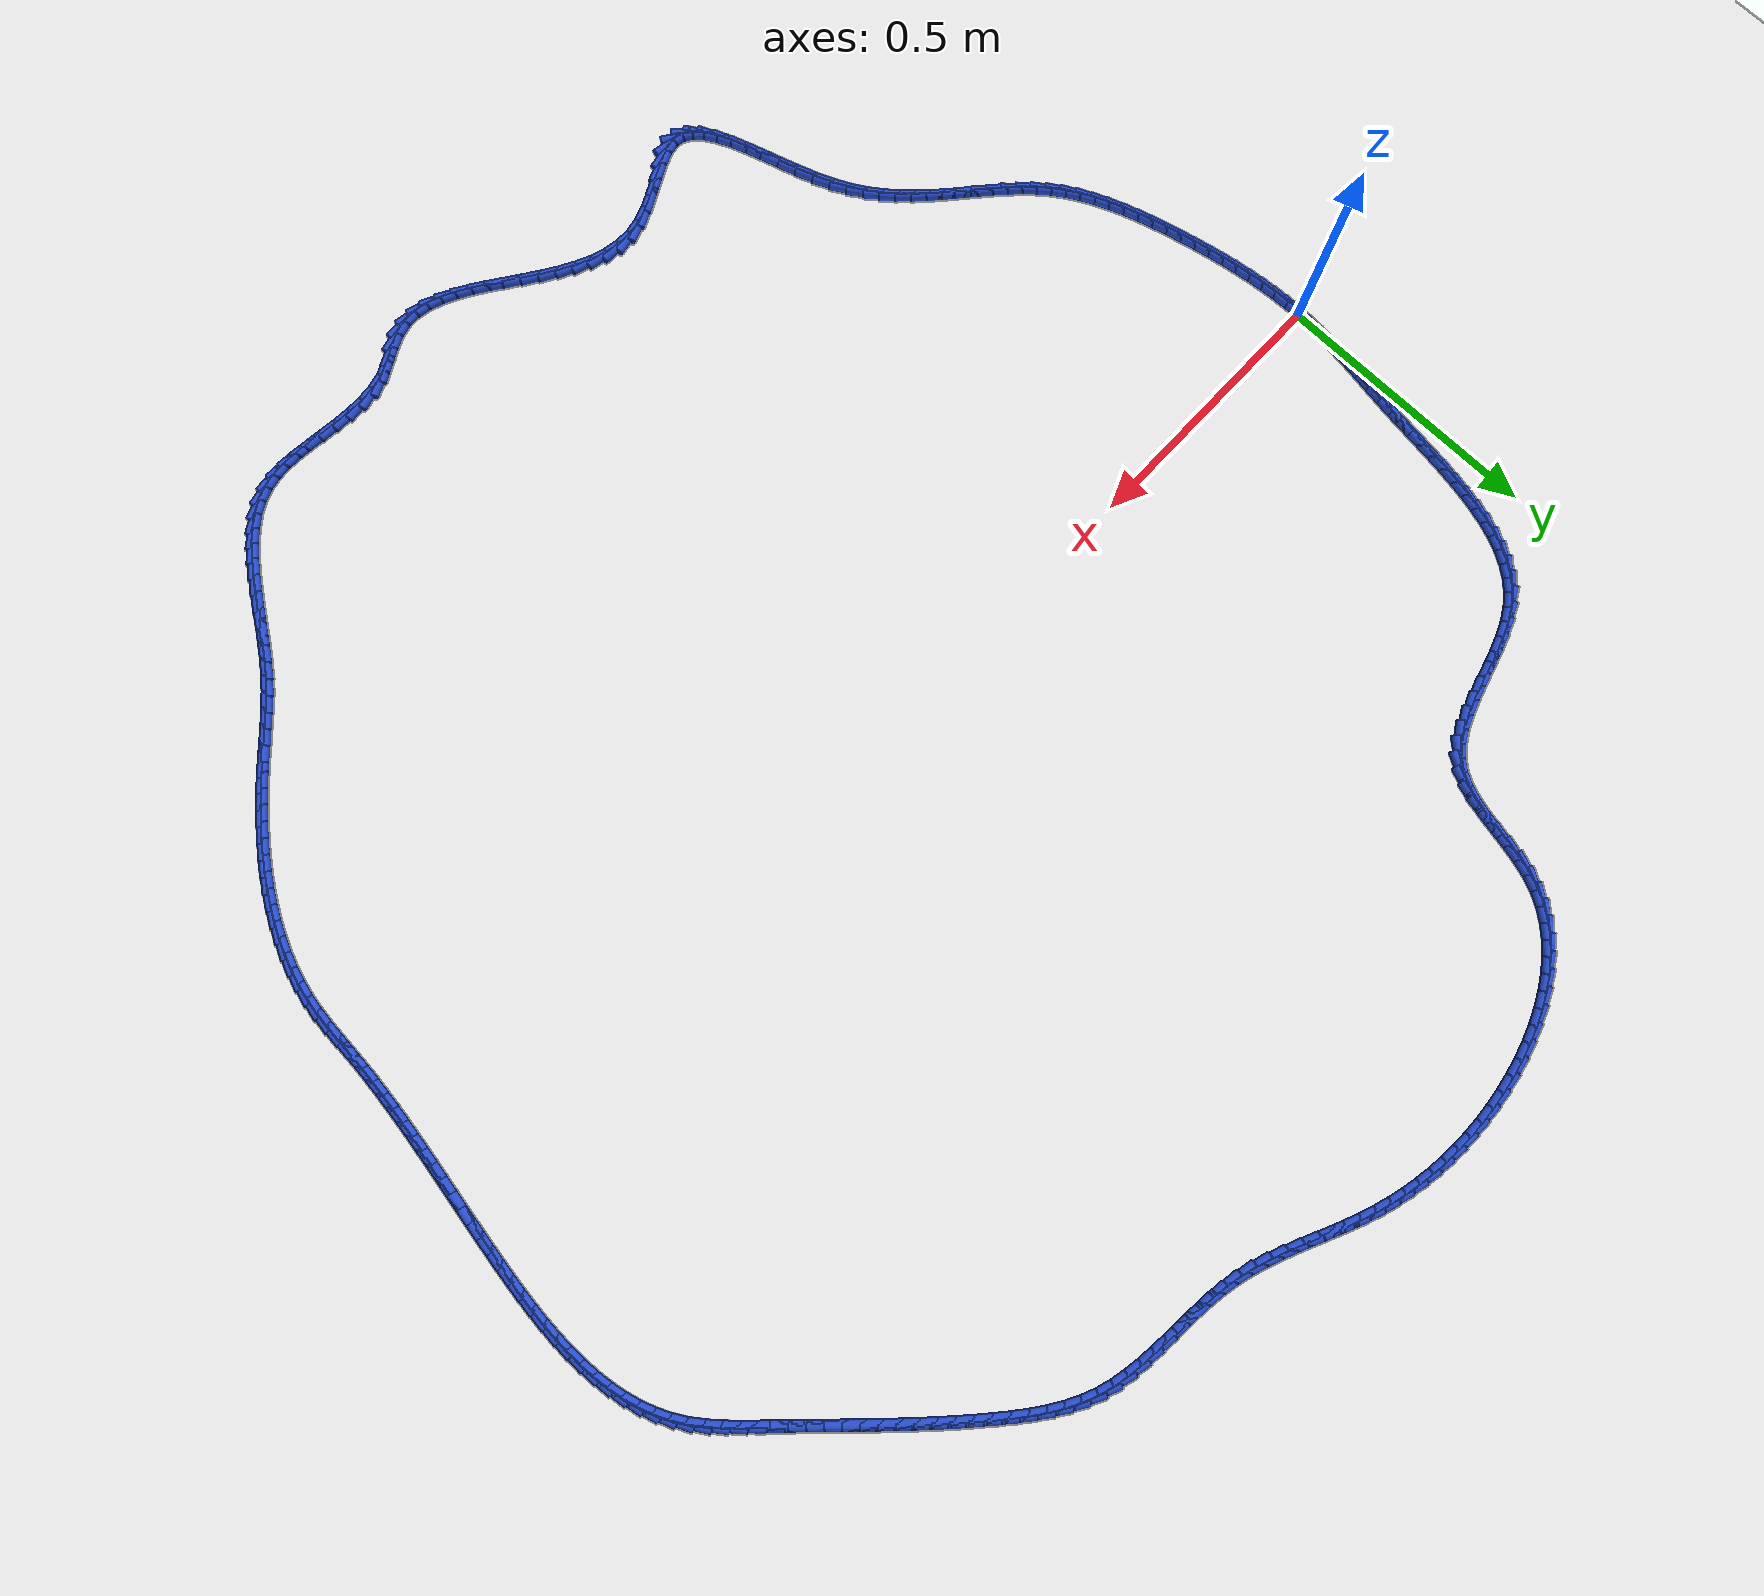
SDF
<sdf version="1.6">
 <world name="default">
  <light name="sun" type="directional">
   <pose>0 0 10 0 -0 0</pose>
   <diffuse>0.8 0.8 0.8 1</diffuse>
   <specular>0.2 0.2 0.2 1</specular>
   <attenuation>
    <range>1000</range>
    <constant>0.9</constant>
    <linear>0.01</linear>
    <quadratic>0.001</quadratic>
   </attenuation>
   <direction>-0.5 0.1 -0.9</direction>
  </light>
  <model name="ground_plane">
   <static>1</static>
   <link name="link">
    <collision name="collision">
     <geometry><plane><normal>0 0 1</normal><size>100 100</size></plane></geometry>
     <surface><friction><ode><mu>100</mu><mu2>50</mu2></ode></friction></surface>
    </collision>
    <visual name="visual">
     <cast_shadows>0</cast_shadows>
     <geometry><plane><normal>0 0 1</normal><size>100 100</size></plane></geometry>
     <material>
      <script><uri>file://media/materials/scripts/gazebo.material</uri><name>Gazebo/WhiteGlow</name></script>
     </material>
    </visual>
   </link>
  </model>
  <gravity>0 0 -9.8</gravity>
  <magnetic_field>6e-06 2.3e-05 -4.2e-05</magnetic_field>
  <atmosphere type="adiabatic"/>
  <physics name="default_physics" default="0" type="ode">
   <max_step_size>0.001</max_step_size>
   <real_time_factor>1</real_time_factor>
   <real_time_update_rate>1000</real_time_update_rate>
  </physics>
  <scene><ambient>0.4 0.4 0.4 1</ambient><background>0.7 0.7 0.7 1</background><shadows>1</shadows></scene>
  <spherical_coordinates>
   <surface_model>EARTH_WGS84</surface_model>
   <latitude_deg>0</latitude_deg>
   <longitude_deg>0</longitude_deg>
   <elevation>0</elevation>
   <heading_deg>0</heading_deg>
  </spherical_coordinates>
  <model name="line">
   <link name="link_0">
    <pose>-2.2551405187698492e-17 7.632783294297951e-17 0.01 0 1.57 1.5288824515302042</pose>
    <collision name="collision">
     <geometry><cylinder><radius>0.01</radius><length>0.08</length></cylinder></geometry>
    </collision>
    <visual name="visual">
     <material>
      <script><name>Gazebo/Blue</name><uri>file://media/materials/scripts/gazebo.material</uri></script>
     </material>
     <geometry><cylinder><radius>0.01</radius><length>0.08</length></cylinder></geometry>
    </visual>
   </link>
   <link name="link_1">
    <pose>0.0011407970177380307 0.027201705684375417 0.01 0 1.57 1.4927546398349003</pose>
    <collision name="collision">
     <geometry><cylinder><radius>0.01</radius><length>0.08</length></cylinder></geometry>
    </collision>
    <visual name="visual">
     <material>
      <script><name>Gazebo/Blue</name><uri>file://media/materials/scripts/gazebo.material</uri></script>
     </material>
     <geometry><cylinder><radius>0.01</radius><length>0.08</length></cylinder></geometry>
    </visual>
   </link>
   <link name="link_2">
    <pose>0.0032627780462168104 0.054336835409915456 0.01 0 1.57 1.4630782804298281</pose>
    <collision name="collision">
     <geometry><cylinder><radius>0.01</radius><length>0.08</length></cylinder></geometry>
    </collision>
    <visual name="visual">
     <material>
      <script><name>Gazebo/Blue</name><uri>file://media/materials/scripts/gazebo.material</uri></script>
     </material>
     <geometry><cylinder><radius>0.01</radius><length>0.08</length></cylinder></geometry>
    </visual>
   </link>
   <link name="link_3">
    <pose>0.0062002938739071645 0.08150169424468343 0.01 0 1.57 1.4400951984167762</pose>
    <collision name="collision">
     <geometry><cylinder><radius>0.01</radius><length>0.08</length></cylinder></geometry>
    </collision>
    <visual name="visual">
     <material>
      <script><name>Gazebo/Blue</name><uri>file://media/materials/scripts/gazebo.material</uri></script>
     </material>
     <geometry><cylinder><radius>0.01</radius><length>0.08</length></cylinder></geometry>
    </visual>
   </link>
   <link name="link_4">
    <pose>0.009787695289279938 0.10879258725674242 0.01 0 1.57 1.4238743431690295</pose>
    <collision name="collision">
     <geometry><cylinder><radius>0.01</radius><length>0.08</length></cylinder></geometry>
    </collision>
    <visual name="visual">
     <material>
      <script><name>Gazebo/Blue</name><uri>file://media/materials/scripts/gazebo.material</uri></script>
     </material>
     <geometry><cylinder><radius>0.01</radius><length>0.08</length></cylinder></geometry>
    </visual>
   </link>
   <link name="link_5">
    <pose>0.013859333080805973 0.13630581951415557 0.01 0 1.57 1.4143445588500612</pose>
    <collision name="collision">
     <geometry><cylinder><radius>0.01</radius><length>0.08</length></cylinder></geometry>
    </collision>
    <visual name="visual">
     <material>
      <script><name>Gazebo/Blue</name><uri>file://media/materials/scripts/gazebo.material</uri></script>
     </material>
     <geometry><cylinder><radius>0.01</radius><length>0.08</length></cylinder></geometry>
    </visual>
   </link>
   <link name="link_6">
    <pose>0.01824955803695613 0.16413769608498616 0.01 0 1.57 1.4113240917865437</pose>
    <collision name="collision">
     <geometry><cylinder><radius>0.01</radius><length>0.08</length></cylinder></geometry>
    </collision>
    <visual name="visual">
     <material>
      <script><name>Gazebo/Blue</name><uri>file://media/materials/scripts/gazebo.material</uri></script>
     </material>
     <geometry><cylinder><radius>0.01</radius><length>0.08</length></cylinder></geometry>
    </visual>
   </link>
   <link name="link_7">
    <pose>0.022792720946201238 0.19238452203729717 0.01 0 1.57 1.4145438455632329</pose>
    <collision name="collision">
     <geometry><cylinder><radius>0.01</radius><length>0.08</length></cylinder></geometry>
    </collision>
    <visual name="visual">
     <material>
      <script><name>Gazebo/Blue</name><uri>file://media/materials/scripts/gazebo.material</uri></script>
     </material>
     <geometry><cylinder><radius>0.01</radius><length>0.08</length></cylinder></geometry>
    </visual>
   </link>
   <link name="link_8">
    <pose>0.027323172597012148 0.22114260243915182 0.01 0 1.57 1.4236632106234344</pose>
    <collision name="collision">
     <geometry><cylinder><radius>0.01</radius><length>0.08</length></cylinder></geometry>
    </collision>
    <visual name="visual">
     <material>
      <script><name>Gazebo/Blue</name><uri>file://media/materials/scripts/gazebo.material</uri></script>
     </material>
     <geometry><cylinder><radius>0.01</radius><length>0.08</length></cylinder></geometry>
    </visual>
   </link>
   <link name="link_9">
    <pose>0.031675279186698053 0.2505082290229851 0.01 0 1.57 1.4353594793840894</pose>
    <collision name="collision">
     <geometry><cylinder><radius>0.01</radius><length>0.08</length></cylinder></geometry>
    </collision>
    <visual name="visual">
     <material>
      <script><name>Gazebo/Blue</name><uri>file://media/materials/scripts/gazebo.material</uri></script>
     </material>
     <geometry><cylinder><radius>0.01</radius><length>0.08</length></cylinder></geometry>
    </visual>
   </link>
   <link name="link_10">
    <pose>0.03576343894935562 0.2805084295396522 0.01 0 1.57 1.4399337824951841</pose>
    <collision name="collision">
     <geometry><cylinder><radius>0.01</radius><length>0.08</length></cylinder></geometry>
    </collision>
    <visual name="visual">
     <material>
      <script><name>Gazebo/Blue</name><uri>file://media/materials/scripts/gazebo.material</uri></script>
     </material>
     <geometry><cylinder><radius>0.01</radius><length>0.08</length></cylinder></geometry>
    </visual>
   </link>
   <link name="link_11">
    <pose>0.03976861907742631 0.31093952878452275 0.01 0 1.57 1.4357670377201683</pose>
    <collision name="collision">
     <geometry><cylinder><radius>0.01</radius><length>0.08</length></cylinder></geometry>
    </collision>
    <visual name="visual">
     <material>
      <script><name>Gazebo/Blue</name><uri>file://media/materials/scripts/gazebo.material</uri></script>
     </material>
     <geometry><cylinder><radius>0.01</radius><length>0.08</length></cylinder></geometry>
    </visual>
   </link>
   <link name="link_12">
    <pose>0.04392721804772479 0.34154987837105244 0.01 0 1.57 1.4229402103571562</pose>
    <collision name="collision">
     <geometry><cylinder><radius>0.01</radius><length>0.08</length></cylinder></geometry>
    </collision>
    <visual name="visual">
     <material>
      <script><name>Gazebo/Blue</name><uri>file://media/materials/scripts/gazebo.material</uri></script>
     </material>
     <geometry><cylinder><radius>0.01</radius><length>0.08</length></cylinder></geometry>
    </visual>
   </link>
   <link name="link_13">
    <pose>0.048475634337065726 0.372087829912697 0.01 0 1.57 1.4011754274274089</pose>
    <collision name="collision">
     <geometry><cylinder><radius>0.01</radius><length>0.08</length></cylinder></geometry>
    </collision>
    <visual name="visual">
     <material>
      <script><name>Gazebo/Blue</name><uri>file://media/materials/scripts/gazebo.material</uri></script>
     </material>
     <geometry><cylinder><radius>0.01</radius><length>0.08</length></cylinder></geometry>
    </visual>
   </link>
   <link name="link_14">
    <pose>0.053650266422263705 0.40230173502291156 0.01 0 1.57 1.3698474683712236</pose>
    <collision name="collision">
     <geometry><cylinder><radius>0.01</radius><length>0.08</length></cylinder></geometry>
    </collision>
    <visual name="visual">
     <material>
      <script><name>Gazebo/Blue</name><uri>file://media/materials/scripts/gazebo.material</uri></script>
     </material>
     <geometry><cylinder><radius>0.01</radius><length>0.08</length></cylinder></geometry>
    </visual>
   </link>
   <link name="link_15">
    <pose>0.05968751278013341 0.43193994531515206 0.01 0 1.57 1.3279898391232734</pose>
    <collision name="collision">
     <geometry><cylinder><radius>0.01</radius><length>0.08</length></cylinder></geometry>
    </collision>
    <visual name="visual">
     <material>
      <script><name>Gazebo/Blue</name><uri>file://media/materials/scripts/gazebo.material</uri></script>
     </material>
     <geometry><cylinder><radius>0.01</radius><length>0.08</length></cylinder></geometry>
    </visual>
   </link>
   <link name="link_16">
    <pose>0.06682377188748949 0.4607508124028741 0.01 0 1.57 1.2743151041964649</pose>
    <collision name="collision">
     <geometry><cylinder><radius>0.01</radius><length>0.08</length></cylinder></geometry>
    </collision>
    <visual name="visual">
     <material>
      <script><name>Gazebo/Blue</name><uri>file://media/materials/scripts/gazebo.material</uri></script>
     </material>
     <geometry><cylinder><radius>0.01</radius><length>0.08</length></cylinder></geometry>
    </visual>
   </link>
   <link name="link_17">
    <pose>0.07529544222114658 0.4884826878995333 0.01 0 1.57 1.207284943718517</pose>
    <collision name="collision">
     <geometry><cylinder><radius>0.01</radius><length>0.08</length></cylinder></geometry>
    </collision>
    <visual name="visual">
     <material>
      <script><name>Gazebo/Blue</name><uri>file://media/materials/scripts/gazebo.material</uri></script>
     </material>
     <geometry><cylinder><radius>0.01</radius><length>0.08</length></cylinder></geometry>
    </visual>
   </link>
   <link name="link_18">
    <pose>0.08533892225791934 0.5148839234185851 0.01 0 1.57 1.1252891621408851</pose>
    <collision name="collision">
     <geometry><cylinder><radius>0.01</radius><length>0.08</length></cylinder></geometry>
    </collision>
    <visual name="visual">
     <material>
      <script><name>Gazebo/Blue</name><uri>file://media/materials/scripts/gazebo.material</uri></script>
     </material>
     <geometry><cylinder><radius>0.01</radius><length>0.08</length></cylinder></geometry>
    </visual>
   </link>
   <link name="link_19">
    <pose>0.09719061047462232 0.5397028705734853 0.01 0 1.57 1.0270154323651437</pose>
    <collision name="collision">
     <geometry><cylinder><radius>0.01</radius><length>0.08</length></cylinder></geometry>
    </collision>
    <visual name="visual">
     <material>
      <script><name>Gazebo/Blue</name><uri>file://media/materials/scripts/gazebo.material</uri></script>
     </material>
     <geometry><cylinder><radius>0.01</radius><length>0.08</length></cylinder></geometry>
    </visual>
   </link>
   <link name="link_20">
    <pose>0.11108690534807034 0.5626878809776895 0.01 0 1.57 0.9120770612071802</pose>
    <collision name="collision">
     <geometry><cylinder><radius>0.01</radius><length>0.08</length></cylinder></geometry>
    </collision>
    <visual name="visual">
     <material>
      <script><name>Gazebo/Blue</name><uri>file://media/materials/scripts/gazebo.material</uri></script>
     </material>
     <geometry><cylinder><radius>0.01</radius><length>0.08</length></cylinder></geometry>
    </visual>
   </link>
   <link name="link_21">
    <pose>0.12726420535507788 0.583587306244653 0.01 0 1.57 0.7818414710279133</pose>
    <collision name="collision">
     <geometry><cylinder><radius>0.01</radius><length>0.08</length></cylinder></geometry>
    </collision>
    <visual name="visual">
     <material>
      <script><name>Gazebo/Blue</name><uri>file://media/materials/scripts/gazebo.material</uri></script>
     </material>
     <geometry><cylinder><radius>0.01</radius><length>0.08</length></cylinder></geometry>
    </visual>
   </link>
   <link name="link_22">
    <pose>0.14595890897245964 0.6021494979878318 0.01 0 1.57 0.6401266976176745</pose>
    <collision name="collision">
     <geometry><cylinder><radius>0.01</radius><length>0.08</length></cylinder></geometry>
    </collision>
    <visual name="visual">
     <material>
      <script><name>Gazebo/Blue</name><uri>file://media/materials/scripts/gazebo.material</uri></script>
     </material>
     <geometry><cylinder><radius>0.01</radius><length>0.08</length></cylinder></geometry>
    </visual>
   </link>
   <link name="link_23">
    <pose>0.16740725675150597 0.6181229570853587 0.01 0 1.57 0.5026025022561849</pose>
    <collision name="collision">
     <geometry><cylinder><radius>0.01</radius><length>0.08</length></cylinder></geometry>
    </collision>
    <visual name="visual">
     <material>
      <script><name>Gazebo/Blue</name><uri>file://media/materials/scripts/gazebo.material</uri></script>
     </material>
     <geometry><cylinder><radius>0.01</radius><length>0.08</length></cylinder></geometry>
    </visual>
   </link>
   <link name="link_24">
    <pose>0.19164470617275342 0.6314459562738525 0.01 0 1.57 0.3994080841491121</pose>
    <collision name="collision">
     <geometry><cylinder><radius>0.01</radius><length>0.08</length></cylinder></geometry>
    </collision>
    <visual name="visual">
     <material>
      <script><name>Gazebo/Blue</name><uri>file://media/materials/scripts/gazebo.material</uri></script>
     </material>
     <geometry><cylinder><radius>0.01</radius><length>0.08</length></cylinder></geometry>
    </visual>
   </link>
   <link name="link_25">
    <pose>0.21811286425857576 0.6426180511943388 0.01 0 1.57 0.3307224995366802</pose>
    <collision name="collision">
     <geometry><cylinder><radius>0.01</radius><length>0.08</length></cylinder></geometry>
    </collision>
    <visual name="visual">
     <material>
      <script><name>Gazebo/Blue</name><uri>file://media/materials/scripts/gazebo.material</uri></script>
     </material>
     <geometry><cylinder><radius>0.01</radius><length>0.08</length></cylinder></geometry>
    </visual>
   </link>
   <link name="link_26">
    <pose>0.24614407206001432 0.6522420711670989 0.01 0 1.57 0.29148200123546625</pose>
    <collision name="collision">
     <geometry><cylinder><radius>0.01</radius><length>0.08</length></cylinder></geometry>
    </collision>
    <visual name="visual">
     <material>
      <script><name>Gazebo/Blue</name><uri>file://media/materials/scripts/gazebo.material</uri></script>
     </material>
     <geometry><cylinder><radius>0.01</radius><length>0.08</length></cylinder></geometry>
    </visual>
   </link>
   <link name="link_27">
    <pose>0.27507067062811036 0.6609208455124145 0.01 0 1.57 0.27850733676640993</pose>
    <collision name="collision">
     <geometry><cylinder><radius>0.01</radius><length>0.08</length></cylinder></geometry>
    </collision>
    <visual name="visual">
     <material>
      <script><name>Gazebo/Blue</name><uri>file://media/materials/scripts/gazebo.material</uri></script>
     </material>
     <geometry><cylinder><radius>0.01</radius><length>0.08</length></cylinder></geometry>
    </visual>
   </link>
   <link name="link_28">
    <pose>0.30422500101390554 0.6692572035505667 0.01 0 1.57 0.2908959764183764</pose>
    <collision name="collision">
     <geometry><cylinder><radius>0.01</radius><length>0.08</length></cylinder></geometry>
    </collision>
    <visual name="visual">
     <material>
      <script><name>Gazebo/Blue</name><uri>file://media/materials/scripts/gazebo.material</uri></script>
     </material>
     <geometry><cylinder><radius>0.01</radius><length>0.08</length></cylinder></geometry>
    </visual>
   </link>
   <link name="link_29">
    <pose>0.33293940426844104 0.6778539746018372 0.01 0 1.57 0.3301294121062424</pose>
    <collision name="collision">
     <geometry><cylinder><radius>0.01</radius><length>0.08</length></cylinder></geometry>
    </collision>
    <visual name="visual">
     <material>
      <script><name>Gazebo/Blue</name><uri>file://media/materials/scripts/gazebo.material</uri></script>
     </material>
     <geometry><cylinder><radius>0.01</radius><length>0.08</length></cylinder></geometry>
    </visual>
   </link>
   <link name="link_30">
    <pose>0.3605462214427583 0.6873139879865076 0.01 0 1.57 0.40015341035838486</pose>
    <collision name="collision">
     <geometry><cylinder><radius>0.01</radius><length>0.08</length></cylinder></geometry>
    </collision>
    <visual name="visual">
     <material>
      <script><name>Gazebo/Blue</name><uri>file://media/materials/scripts/gazebo.material</uri></script>
     </material>
     <geometry><cylinder><radius>0.01</radius><length>0.08</length></cylinder></geometry>
    </visual>
   </link>
   <link name="link_31">
    <pose>0.38637779358789853 0.6982400730248589 0.01 0 1.57 0.5071403715740864</pose>
    <collision name="collision">
     <geometry><cylinder><radius>0.01</radius><length>0.08</length></cylinder></geometry>
    </collision>
    <visual name="visual">
     <material>
      <script><name>Gazebo/Blue</name><uri>file://media/materials/scripts/gazebo.material</uri></script>
     </material>
     <geometry><cylinder><radius>0.01</radius><length>0.08</length></cylinder></geometry>
    </visual>
   </link>
   <link name="link_32">
    <pose>0.4097664617549033 0.7112350590371729 0.01 0 1.57 0.6578043464636418</pose>
    <collision name="collision">
     <geometry><cylinder><radius>0.01</radius><length>0.08</length></cylinder></geometry>
    </collision>
    <visual name="visual">
     <material>
      <script><name>Gazebo/Blue</name><uri>file://media/materials/scripts/gazebo.material</uri></script>
     </material>
     <geometry><cylinder><radius>0.01</radius><length>0.08</length></cylinder></geometry>
    </visual>
   </link>
   <link name="link_33">
    <pose>0.4300445669948138 0.726901775343731 0.01 0 1.57 0.8539025543426916</pose>
    <collision name="collision">
     <geometry><cylinder><radius>0.01</radius><length>0.08</length></cylinder></geometry>
    </collision>
    <visual name="visual">
     <material>
      <script><name>Gazebo/Blue</name><uri>file://media/materials/scripts/gazebo.material</uri></script>
     </material>
     <geometry><cylinder><radius>0.01</radius><length>0.08</length></cylinder></geometry>
    </visual>
   </link>
   <link name="link_34">
    <pose>0.4465497264667318 0.7458386767341181 0.01 0 1.57 1.0576159487594454</pose>
    <collision name="collision">
     <geometry><cylinder><radius>0.01</radius><length>0.08</length></cylinder></geometry>
    </collision>
    <visual name="visual">
     <material>
      <script><name>Gazebo/Blue</name><uri>file://media/materials/scripts/gazebo.material</uri></script>
     </material>
     <geometry><cylinder><radius>0.01</radius><length>0.08</length></cylinder></geometry>
    </visual>
   </link>
   <link name="link_35">
    <pose>0.45915255733565113 0.7682022966308191 0.01 0 1.57 1.2075177611733987</pose>
    <collision name="collision">
     <geometry><cylinder><radius>0.01</radius><length>0.08</length></cylinder></geometry>
    </collision>
    <visual name="visual">
     <material>
      <script><name>Gazebo/Blue</name><uri>file://media/materials/scripts/gazebo.material</uri></script>
     </material>
     <geometry><cylinder><radius>0.01</radius><length>0.08</length></cylinder></geometry>
    </visual>
   </link>
   <link name="link_36">
    <pose>0.4687064988021745 0.7933342903084951 0.01 0 1.57 1.30253170234999</pose>
    <collision name="collision">
     <geometry><cylinder><radius>0.01</radius><length>0.08</length></cylinder></geometry>
    </collision>
    <visual name="visual">
     <material>
      <script><name>Gazebo/Blue</name><uri>file://media/materials/scripts/gazebo.material</uri></script>
     </material>
     <geometry><cylinder><radius>0.01</radius><length>0.08</length></cylinder></geometry>
    </visual>
   </link>
   <link name="link_37">
    <pose>0.4761709323238113 0.8204884741178128 0.01 0 1.57 1.351574828118892</pose>
    <collision name="collision">
     <geometry><cylinder><radius>0.01</radius><length>0.08</length></cylinder></geometry>
    </collision>
    <visual name="visual">
     <material>
      <script><name>Gazebo/Blue</name><uri>file://media/materials/scripts/gazebo.material</uri></script>
     </material>
     <geometry><cylinder><radius>0.01</radius><length>0.08</length></cylinder></geometry>
    </visual>
   </link>
   <link name="link_38">
    <pose>0.4825052393580709 0.8489186644094397 0.01 0 1.57 1.3610951331240515</pose>
    <collision name="collision">
     <geometry><cylinder><radius>0.01</radius><length>0.08</length></cylinder></geometry>
    </collision>
    <visual name="visual">
     <material>
      <script><name>Gazebo/Blue</name><uri>file://media/materials/scripts/gazebo.material</uri></script>
     </material>
     <geometry><cylinder><radius>0.01</radius><length>0.08</length></cylinder></geometry>
    </visual>
   </link>
   <link name="link_39">
    <pose>0.4886688013624628 0.877878677534043 0.01 0 1.57 1.3334848886120183</pose>
    <collision name="collision">
     <geometry><cylinder><radius>0.01</radius><length>0.08</length></cylinder></geometry>
    </collision>
    <visual name="visual">
     <material>
      <script><name>Gazebo/Blue</name><uri>file://media/materials/scripts/gazebo.material</uri></script>
     </material>
     <geometry><cylinder><radius>0.01</radius><length>0.08</length></cylinder></geometry>
    </visual>
   </link>
   <link name="link_40">
    <pose>0.4956209997944965 0.9066223298422902 0.01 0 1.57 1.2673009613841848</pose>
    <collision name="collision">
     <geometry><cylinder><radius>0.01</radius><length>0.08</length></cylinder></geometry>
    </collision>
    <visual name="visual">
     <material>
      <script><name>Gazebo/Blue</name><uri>file://media/materials/scripts/gazebo.material</uri></script>
     </material>
     <geometry><cylinder><radius>0.01</radius><length>0.08</length></cylinder></geometry>
    </visual>
   </link>
   <link name="link_41">
    <pose>0.5043212161116815 0.9344034376848478 0.01 0 1.57 1.1602106038765794</pose>
    <collision name="collision">
     <geometry><cylinder><radius>0.01</radius><length>0.08</length></cylinder></geometry>
    </collision>
    <visual name="visual">
     <material>
      <script><name>Gazebo/Blue</name><uri>file://media/materials/scripts/gazebo.material</uri></script>
     </material>
     <geometry><cylinder><radius>0.01</radius><length>0.08</length></cylinder></geometry>
    </visual>
   </link>
   <link name="link_42">
    <pose>0.5156839773709774 0.9605050616831939 0.01 0 1.57 1.036266361393758</pose>
    <collision name="collision">
     <geometry><cylinder><radius>0.01</radius><length>0.08</length></cylinder></geometry>
    </collision>
    <visual name="visual">
     <material>
      <script><name>Gazebo/Blue</name><uri>file://media/materials/scripts/gazebo.material</uri></script>
     </material>
     <geometry><cylinder><radius>0.01</radius><length>0.08</length></cylinder></geometry>
    </visual>
   </link>
   <link name="link_43">
    <pose>0.5299701821667856 0.9846364165826844 0.01 0 1.57 0.9177967141740887</pose>
    <collision name="collision">
     <geometry><cylinder><radius>0.01</radius><length>0.08</length></cylinder></geometry>
    </collision>
    <visual name="visual">
     <material>
      <script><name>Gazebo/Blue</name><uri>file://media/materials/scripts/gazebo.material</uri></script>
     </material>
     <geometry><cylinder><radius>0.01</radius><length>0.08</length></cylinder></geometry>
    </visual>
   </link>
   <link name="link_44">
    <pose>0.5469463803943242 1.0068290236817978 0.01 0 1.57 0.8073723883056089</pose>
    <collision name="collision">
     <geometry><cylinder><radius>0.01</radius><length>0.08</length></cylinder></geometry>
    </collision>
    <visual name="visual">
     <material>
      <script><name>Gazebo/Blue</name><uri>file://media/materials/scripts/gazebo.material</uri></script>
     </material>
     <geometry><cylinder><radius>0.01</radius><length>0.08</length></cylinder></geometry>
    </visual>
   </link>
   <link name="link_45">
    <pose>0.566366904526244 1.0271223698210732 0.01 0 1.57 0.7060298740020946</pose>
    <collision name="collision">
     <geometry><cylinder><radius>0.01</radius><length>0.08</length></cylinder></geometry>
    </collision>
    <visual name="visual">
     <material>
      <script><name>Gazebo/Blue</name><uri>file://media/materials/scripts/gazebo.material</uri></script>
     </material>
     <geometry><cylinder><radius>0.01</radius><length>0.08</length></cylinder></geometry>
    </visual>
   </link>
   <link name="link_46">
    <pose>0.587986087035196 1.0455559418410505 0.01 0 1.57 0.6139293248139052</pose>
    <collision name="collision">
     <geometry><cylinder><radius>0.01</radius><length>0.08</length></cylinder></geometry>
    </collision>
    <visual name="visual">
     <material>
      <script><name>Gazebo/Blue</name><uri>file://media/materials/scripts/gazebo.material</uri></script>
     </material>
     <geometry><cylinder><radius>0.01</radius><length>0.08</length></cylinder></geometry>
    </visual>
   </link>
   <link name="link_47">
    <pose>0.6115582603938308 1.062169226582269 0.01 0 1.57 0.5306122185136694</pose>
    <collision name="collision">
     <geometry><cylinder><radius>0.01</radius><length>0.08</length></cylinder></geometry>
    </collision>
    <visual name="visual">
     <material>
      <script><name>Gazebo/Blue</name><uri>file://media/materials/scripts/gazebo.material</uri></script>
     </material>
     <geometry><cylinder><radius>0.01</radius><length>0.08</length></cylinder></geometry>
    </visual>
   </link>
   <link name="link_48">
    <pose>0.6368377570747994 1.0770017108852679 0.01 0 1.57 0.45525390661103365</pose>
    <collision name="collision">
     <geometry><cylinder><radius>0.01</radius><length>0.08</length></cylinder></geometry>
    </collision>
    <visual name="visual">
     <material>
      <script><name>Gazebo/Blue</name><uri>file://media/materials/scripts/gazebo.material</uri></script>
     </material>
     <geometry><cylinder><radius>0.01</radius><length>0.08</length></cylinder></geometry>
    </visual>
   </link>
   <link name="link_49">
    <pose>0.6635789095507525 1.0900928815905857 0.01 0 1.57 0.386857241301085</pose>
    <collision name="collision">
     <geometry><cylinder><radius>0.01</radius><length>0.08</length></cylinder></geometry>
    </collision>
    <visual name="visual">
     <material>
      <script><name>Gazebo/Blue</name><uri>file://media/materials/scripts/gazebo.material</uri></script>
     </material>
     <geometry><cylinder><radius>0.01</radius><length>0.08</length></cylinder></geometry>
    </visual>
   </link>
   <link name="link_50">
    <pose>0.6915360502943412 1.101482225538763 0.01 0 1.57 0.3243777602206729</pose>
    <collision name="collision">
     <geometry><cylinder><radius>0.01</radius><length>0.08</length></cylinder></geometry>
    </collision>
    <visual name="visual">
     <material>
      <script><name>Gazebo/Blue</name><uri>file://media/materials/scripts/gazebo.material</uri></script>
     </material>
     <geometry><cylinder><radius>0.01</radius><length>0.08</length></cylinder></geometry>
    </visual>
   </link>
   <link name="link_51">
    <pose>0.7204635117782157 1.111209229570338 0.01 0 1.57 0.26679220355363736</pose>
    <collision name="collision">
     <geometry><cylinder><radius>0.01</radius><length>0.08</length></cylinder></geometry>
    </collision>
    <visual name="visual">
     <material>
      <script><name>Gazebo/Blue</name><uri>file://media/materials/scripts/gazebo.material</uri></script>
     </material>
     <geometry><cylinder><radius>0.01</radius><length>0.08</length></cylinder></geometry>
    </visual>
   </link>
   <link name="link_52">
    <pose>0.7501156264750274 1.1193133805258506 0.01 0 1.57 0.21312706283663427</pose>
    <collision name="collision">
     <geometry><cylinder><radius>0.01</radius><length>0.08</length></cylinder></geometry>
    </collision>
    <visual name="visual">
     <material>
      <script><name>Gazebo/Blue</name><uri>file://media/materials/scripts/gazebo.material</uri></script>
     </material>
     <geometry><cylinder><radius>0.01</radius><length>0.08</length></cylinder></geometry>
    </visual>
   </link>
   <link name="link_53">
    <pose>0.7802467268574268 1.12583416524584 0.01 0 1.57 0.16246126451664947</pose>
    <collision name="collision">
     <geometry><cylinder><radius>0.01</radius><length>0.08</length></cylinder></geometry>
    </collision>
    <visual name="visual">
     <material>
      <script><name>Gazebo/Blue</name><uri>file://media/materials/scripts/gazebo.material</uri></script>
     </material>
     <geometry><cylinder><radius>0.01</radius><length>0.08</length></cylinder></geometry>
    </visual>
   </link>
   <link name="link_54">
    <pose>0.8106111453980649 1.1308110705708454 0.01 0 1.57 0.11391249476696579</pose>
    <collision name="collision">
     <geometry><cylinder><radius>0.01</radius><length>0.08</length></cylinder></geometry>
    </collision>
    <visual name="visual">
     <material>
      <script><name>Gazebo/Blue</name><uri>file://media/materials/scripts/gazebo.material</uri></script>
     </material>
     <geometry><cylinder><radius>0.01</radius><length>0.08</length></cylinder></geometry>
    </visual>
   </link>
   <link name="link_55">
    <pose>0.8409632145695928 1.134283583341406 0.01 0 1.57 0.06661239130415425</pose>
    <collision name="collision">
     <geometry><cylinder><radius>0.01</radius><length>0.08</length></cylinder></geometry>
    </collision>
    <visual name="visual">
     <material>
      <script><name>Gazebo/Blue</name><uri>file://media/materials/scripts/gazebo.material</uri></script>
     </material>
     <geometry><cylinder><radius>0.01</radius><length>0.08</length></cylinder></geometry>
    </visual>
   </link>
   <link name="link_56">
    <pose>0.8710572668446603 1.1362911903980608 0.01 0 1.57 0.019647832347006882</pose>
    <collision name="collision">
     <geometry><cylinder><radius>0.01</radius><length>0.08</length></cylinder></geometry>
    </collision>
    <visual name="visual">
     <material>
      <script><name>Gazebo/Blue</name><uri>file://media/materials/scripts/gazebo.material</uri></script>
     </material>
     <geometry><cylinder><radius>0.01</radius><length>0.08</length></cylinder></geometry>
    </visual>
   </link>
   <link name="link_57">
    <pose>0.900659563511931 1.1368728862140893 0.01 0 1.57 -0.027949812320081664</pose>
    <collision name="collision">
     <geometry><cylinder><radius>0.01</radius><length>0.08</length></cylinder></geometry>
    </collision>
    <visual name="visual">
     <material>
      <script><name>Gazebo/Blue</name><uri>file://media/materials/scripts/gazebo.material</uri></script>
     </material>
     <geometry><cylinder><radius>0.01</radius><length>0.08</length></cylinder></geometry>
    </visual>
   </link>
   <link name="link_58">
    <pose>0.9296933287044586 1.136061186550574 0.01 0 1.57 -0.07624535942908973</pose>
    <collision name="collision">
     <geometry><cylinder><radius>0.01</radius><length>0.08</length></cylinder></geometry>
    </collision>
    <visual name="visual">
     <material>
      <script><name>Gazebo/Blue</name><uri>file://media/materials/scripts/gazebo.material</uri></script>
     </material>
     <geometry><cylinder><radius>0.01</radius><length>0.08</length></cylinder></geometry>
    </visual>
   </link>
   <link name="link_59">
    <pose>0.9581924739721214 1.133884038495547 0.01 0 1.57 -0.1248701350980151</pose>
    <collision name="collision">
     <geometry><cylinder><radius>0.01</radius><length>0.08</length></cylinder></geometry>
    </collision>
    <visual name="visual">
     <material>
      <script><name>Gazebo/Blue</name><uri>file://media/materials/scripts/gazebo.material</uri></script>
     </material>
     <geometry><cylinder><radius>0.01</radius><length>0.08</length></cylinder></geometry>
    </visual>
   </link>
   <link name="link_60">
    <pose>0.9861932291538245 1.1303692934486158 0.01 0 1.57 -0.17343016236885703</pose>
    <collision name="collision">
     <geometry><cylinder><radius>0.01</radius><length>0.08</length></cylinder></geometry>
    </collision>
    <visual name="visual">
     <material>
      <script><name>Gazebo/Blue</name><uri>file://media/materials/scripts/gazebo.material</uri></script>
     </material>
     <geometry><cylinder><radius>0.01</radius><length>0.08</length></cylinder></geometry>
    </visual>
   </link>
   <link name="link_61">
    <pose>1.0137318240884738 1.1255448028093875 0.01 0 1.57 -0.2215263073344703</pose>
    <collision name="collision">
     <geometry><cylinder><radius>0.01</radius><length>0.08</length></cylinder></geometry>
    </collision>
    <visual name="visual">
     <material>
      <script><name>Gazebo/Blue</name><uri>file://media/materials/scripts/gazebo.material</uri></script>
     </material>
     <geometry><cylinder><radius>0.01</radius><length>0.08</length></cylinder></geometry>
    </visual>
   </link>
   <link name="link_62">
    <pose>1.0408444886149748 1.119438417977469 0.01 0 1.57 -0.26877016621185135</pose>
    <collision name="collision">
     <geometry><cylinder><radius>0.01</radius><length>0.08</length></cylinder></geometry>
    </collision>
    <visual name="visual">
     <material>
      <script><name>Gazebo/Blue</name><uri>file://media/materials/scripts/gazebo.material</uri></script>
     </material>
     <geometry><cylinder><radius>0.01</radius><length>0.08</length></cylinder></geometry>
    </visual>
   </link>
   <link name="link_63">
    <pose>1.0675674525722323 1.1120779903524673 0.01 0 1.57 -0.31479889620635837</pose>
    <collision name="collision">
     <geometry><cylinder><radius>0.01</radius><length>0.08</length></cylinder></geometry>
    </collision>
    <visual name="visual">
     <material>
      <script><name>Gazebo/Blue</name><uri>file://media/materials/scripts/gazebo.material</uri></script>
     </material>
     <geometry><cylinder><radius>0.01</radius><length>0.08</length></cylinder></geometry>
    </visual>
   </link>
   <link name="link_64">
    <pose>1.0939369457991517 1.1034913713339898 0.01 0 1.57 -0.35920142715494563</pose>
    <collision name="collision">
     <geometry><cylinder><radius>0.01</radius><length>0.08</length></cylinder></geometry>
    </collision>
    <visual name="visual">
     <material>
      <script><name>Gazebo/Blue</name><uri>file://media/materials/scripts/gazebo.material</uri></script>
     </material>
     <geometry><cylinder><radius>0.01</radius><length>0.08</length></cylinder></geometry>
    </visual>
   </link>
   <link name="link_65">
    <pose>1.1199896726734568 1.0937087961470224 0.01 0 1.57 -0.39693983732204374</pose>
    <collision name="collision">
     <geometry><cylinder><radius>0.01</radius><length>0.08</length></cylinder></geometry>
    </collision>
    <visual name="visual">
     <material>
      <script><name>Gazebo/Blue</name><uri>file://media/materials/scripts/gazebo.material</uri></script>
     </material>
     <geometry><cylinder><radius>0.01</radius><length>0.08</length></cylinder></geometry>
    </visual>
   </link>
   <link name="link_66">
    <pose>1.1457889119491418 1.0828939952546732 0.01 0 1.57 -0.420892536509313</pose>
    <collision name="collision">
     <geometry><cylinder><radius>0.01</radius><length>0.08</length></cylinder></geometry>
    </collision>
    <visual name="visual">
     <material>
      <script><name>Gazebo/Blue</name><uri>file://media/materials/scripts/gazebo.material</uri></script>
     </material>
     <geometry><cylinder><radius>0.01</radius><length>0.08</length></cylinder></geometry>
    </visual>
   </link>
   <link name="link_67">
    <pose>1.1714380768957648 1.0714123131356583 0.01 0 1.57 -0.430745317962416</pose>
    <collision name="collision">
     <geometry><cylinder><radius>0.01</radius><length>0.08</length></cylinder></geometry>
    </collision>
    <visual name="visual">
     <material>
      <script><name>Gazebo/Blue</name><uri>file://media/materials/scripts/gazebo.material</uri></script>
     </material>
     <geometry><cylinder><radius>0.01</radius><length>0.08</length></cylinder></geometry>
    </visual>
   </link>
   <link name="link_68">
    <pose>1.197043912701138 1.0596458320169777 0.01 0 1.57 -0.42667127711675795</pose>
    <collision name="collision">
     <geometry><cylinder><radius>0.01</radius><length>0.08</length></cylinder></geometry>
    </collision>
    <visual name="visual">
     <material>
      <script><name>Gazebo/Blue</name><uri>file://media/materials/scripts/gazebo.material</uri></script>
     </material>
     <geometry><cylinder><radius>0.01</radius><length>0.08</length></cylinder></geometry>
    </visual>
   </link>
   <link name="link_69">
    <pose>1.2227131645530749 1.047976634125632 0.01 0 1.57 -0.4086716947445242</pose>
    <collision name="collision">
     <geometry><cylinder><radius>0.01</radius><length>0.08</length></cylinder></geometry>
    </collision>
    <visual name="visual">
     <material>
      <script><name>Gazebo/Blue</name><uri>file://media/materials/scripts/gazebo.material</uri></script>
     </material>
     <geometry><cylinder><radius>0.01</radius><length>0.08</length></cylinder></geometry>
    </visual>
   </link>
   <link name="link_70">
    <pose>1.248552577639388 1.0367868016886217 0.01 0 1.57 -0.3766005412703607</pose>
    <collision name="collision">
     <geometry><cylinder><radius>0.01</radius><length>0.08</length></cylinder></geometry>
    </collision>
    <visual name="visual">
     <material>
      <script><name>Gazebo/Blue</name><uri>file://media/materials/scripts/gazebo.material</uri></script>
     </material>
     <geometry><cylinder><radius>0.01</radius><length>0.08</length></cylinder></geometry>
    </visual>
   </link>
   <link name="link_71">
    <pose>1.2746688971478892 1.026458416932946 0.01 0 1.57 -0.3302686686060403</pose>
    <collision name="collision">
     <geometry><cylinder><radius>0.01</radius><length>0.08</length></cylinder></geometry>
    </collision>
    <visual name="visual">
     <material>
      <script><name>Gazebo/Blue</name><uri>file://media/materials/scripts/gazebo.material</uri></script>
     </material>
     <geometry><cylinder><radius>0.01</radius><length>0.08</length></cylinder></geometry>
    </visual>
   </link>
   <link name="link_72">
    <pose>1.301168868266392 1.017373562085606 0.01 0 1.57 -0.26963650728713723</pose>
    <collision name="collision">
     <geometry><cylinder><radius>0.01</radius><length>0.08</length></cylinder></geometry>
    </collision>
    <visual name="visual">
     <material>
      <script><name>Gazebo/Blue</name><uri>file://media/materials/scripts/gazebo.material</uri></script>
     </material>
     <geometry><cylinder><radius>0.01</radius><length>0.08</length></cylinder></geometry>
    </visual>
   </link>
   <link name="link_73">
    <pose>1.3281592361827086 1.0099143193736018 0.01 0 1.57 -0.20021347893387959</pose>
    <collision name="collision">
     <geometry><cylinder><radius>0.01</radius><length>0.08</length></cylinder></geometry>
    </collision>
    <visual name="visual">
     <material>
      <script><name>Gazebo/Blue</name><uri>file://media/materials/scripts/gazebo.material</uri></script>
     </material>
     <geometry><cylinder><radius>0.01</radius><length>0.08</length></cylinder></geometry>
    </visual>
   </link>
   <link name="link_74">
    <pose>1.3557046515025295 1.004324464992871 0.01 0 1.57 -0.14340314209981983</pose>
    <collision name="collision">
     <geometry><cylinder><radius>0.01</radius><length>0.08</length></cylinder></geometry>
    </collision>
    <visual name="visual">
     <material>
      <script><name>Gazebo/Blue</name><uri>file://media/materials/scripts/gazebo.material</uri></script>
     </material>
     <geometry><cylinder><radius>0.01</radius><length>0.08</length></cylinder></geometry>
    </visual>
   </link>
   <link name="link_75">
    <pose>1.3836976970121337 1.0002824288174226 0.01 0 1.57 -0.1042615870564046</pose>
    <collision name="collision">
     <geometry><cylinder><radius>0.01</radius><length>0.08</length></cylinder></geometry>
    </collision>
    <visual name="visual">
     <material>
      <script><name>Gazebo/Blue</name><uri>file://media/materials/scripts/gazebo.material</uri></script>
     </material>
     <geometry><cylinder><radius>0.01</radius><length>0.08</length></cylinder></geometry>
    </visual>
   </link>
   <link name="link_76">
    <pose>1.411986996048947 0.9973222074808779 0.01 0 1.57 -0.08226434981564956</pose>
    <collision name="collision">
     <geometry><cylinder><radius>0.01</radius><length>0.08</length></cylinder></geometry>
    </collision>
    <visual name="visual">
     <material>
      <script><name>Gazebo/Blue</name><uri>file://media/materials/scripts/gazebo.material</uri></script>
     </material>
     <geometry><cylinder><radius>0.01</radius><length>0.08</length></cylinder></geometry>
    </visual>
   </link>
   <link name="link_77">
    <pose>1.4404211719341693 0.9949777975635512 0.01 0 1.57 -0.07704666643448888</pose>
    <collision name="collision">
     <geometry><cylinder><radius>0.01</radius><length>0.08</length></cylinder></geometry>
    </collision>
    <visual name="visual">
     <material>
      <script><name>Gazebo/Blue</name><uri>file://media/materials/scripts/gazebo.material</uri></script>
     </material>
     <geometry><cylinder><radius>0.01</radius><length>0.08</length></cylinder></geometry>
    </visual>
   </link>
   <link name="link_78">
    <pose>1.4688488479890012 0.9927831956457573 0.01 0 1.57 -0.08858310139092127</pose>
    <collision name="collision">
     <geometry><cylinder><radius>0.01</radius><length>0.08</length></cylinder></geometry>
    </collision>
    <visual name="visual">
     <material>
      <script><name>Gazebo/Blue</name><uri>file://media/materials/scripts/gazebo.material</uri></script>
     </material>
     <geometry><cylinder><radius>0.01</radius><length>0.08</length></cylinder></geometry>
    </visual>
   </link>
   <link name="link_79">
    <pose>1.4971186475346436 0.9902723983078104 0.01 0 1.57 -0.1172329205561936</pose>
    <collision name="collision">
     <geometry><cylinder><radius>0.01</radius><length>0.08</length></cylinder></geometry>
    </collision>
    <visual name="visual">
     <material>
      <script><name>Gazebo/Blue</name><uri>file://media/materials/scripts/gazebo.material</uri></script>
     </material>
     <geometry><cylinder><radius>0.01</radius><length>0.08</length></cylinder></geometry>
    </visual>
   </link>
   <link name="link_80">
    <pose>1.525079193892298 0.9869794021300259 0.01 0 1.57 -0.16365802836264334</pose>
    <collision name="collision">
     <geometry><cylinder><radius>0.01</radius><length>0.08</length></cylinder></geometry>
    </collision>
    <visual name="visual">
     <material>
      <script><name>Gazebo/Blue</name><uri>file://media/materials/scripts/gazebo.material</uri></script>
     </material>
     <geometry><cylinder><radius>0.01</radius><length>0.08</length></cylinder></geometry>
    </visual>
   </link>
   <link name="link_81">
    <pose>1.5525791103831634 0.9824382036927174 0.01 0 1.57 -0.2285813809524016</pose>
    <collision name="collision">
     <geometry><cylinder><radius>0.01</radius><length>0.08</length></cylinder></geometry>
    </collision>
    <visual name="visual">
     <material>
      <script><name>Gazebo/Blue</name><uri>file://media/materials/scripts/gazebo.material</uri></script>
     </material>
     <geometry><cylinder><radius>0.01</radius><length>0.08</length></cylinder></geometry>
    </visual>
   </link>
   <link name="link_82">
    <pose>1.5794670203284418 0.9761827995761999 0.01 0 1.57 -0.3123314726011857</pose>
    <collision name="collision">
     <geometry><cylinder><radius>0.01</radius><length>0.08</length></cylinder></geometry>
    </collision>
    <visual name="visual">
     <material>
      <script><name>Gazebo/Blue</name><uri>file://media/materials/scripts/gazebo.material</uri></script>
     </material>
     <geometry><cylinder><radius>0.01</radius><length>0.08</length></cylinder></geometry>
    </visual>
   </link>
   <link name="link_83">
    <pose>1.6055915470493338 0.967747186360788 0.01 0 1.57 -0.4108900697118907</pose>
    <collision name="collision">
     <geometry><cylinder><radius>0.01</radius><length>0.08</length></cylinder></geometry>
    </collision>
    <visual name="visual">
     <material>
      <script><name>Gazebo/Blue</name><uri>file://media/materials/scripts/gazebo.material</uri></script>
     </material>
     <geometry><cylinder><radius>0.01</radius><length>0.08</length></cylinder></geometry>
    </visual>
   </link>
   <link name="link_84">
    <pose>1.6308242399019675 0.956753558900686 0.01 0 1.57 -0.5016200299486727</pose>
    <collision name="collision">
     <geometry><cylinder><radius>0.01</radius><length>0.08</length></cylinder></geometry>
    </collision>
    <visual name="visual">
     <material>
      <script><name>Gazebo/Blue</name><uri>file://media/materials/scripts/gazebo.material</uri></script>
     </material>
     <geometry><cylinder><radius>0.01</radius><length>0.08</length></cylinder></geometry>
    </visual>
   </link>
   <link name="link_85">
    <pose>1.6551847936858874 0.9433940393155402 0.01 0 1.57 -0.5760219329005849</pose>
    <collision name="collision">
     <geometry><cylinder><radius>0.01</radius><length>0.08</length></cylinder></geometry>
    </collision>
    <visual name="visual">
     <material>
      <script><name>Gazebo/Blue</name><uri>file://media/materials/scripts/gazebo.material</uri></script>
     </material>
     <geometry><cylinder><radius>0.01</radius><length>0.08</length></cylinder></geometry>
    </visual>
   </link>
   <link name="link_86">
    <pose>1.6787517990551546 0.9280873267464477 0.01 0 1.57 -0.6349180226319622</pose>
    <collision name="collision">
     <geometry><cylinder><radius>0.01</radius><length>0.08</length></cylinder></geometry>
    </collision>
    <visual name="visual">
     <material>
      <script><name>Gazebo/Blue</name><uri>file://media/materials/scripts/gazebo.material</uri></script>
     </material>
     <geometry><cylinder><radius>0.01</radius><length>0.08</length></cylinder></geometry>
    </visual>
   </link>
   <link name="link_87">
    <pose>1.7016039968390235 0.9112526980703763 0.01 0 1.57 -0.6793993611296293</pose>
    <collision name="collision">
     <geometry><cylinder><radius>0.01</radius><length>0.08</length></cylinder></geometry>
    </collision>
    <visual name="visual">
     <material>
      <script><name>Gazebo/Blue</name><uri>file://media/materials/scripts/gazebo.material</uri></script>
     </material>
     <geometry><cylinder><radius>0.01</radius><length>0.08</length></cylinder></geometry>
    </visual>
   </link>
   <link name="link_88">
    <pose>1.7238201278667469 0.8933094301642939 0.01 0 1.57 -0.7104317668136934</pose>
    <collision name="collision">
     <geometry><cylinder><radius>0.01</radius><length>0.08</length></cylinder></geometry>
    </collision>
    <visual name="visual">
     <material>
      <script><name>Gazebo/Blue</name><uri>file://media/materials/scripts/gazebo.material</uri></script>
     </material>
     <geometry><cylinder><radius>0.01</radius><length>0.08</length></cylinder></geometry>
    </visual>
   </link>
   <link name="link_89">
    <pose>1.7454789329675786 0.8746767999051679 0.01 0 1.57 -0.7296650820612394</pose>
    <collision name="collision">
     <geometry><cylinder><radius>0.01</radius><length>0.08</length></cylinder></geometry>
    </collision>
    <visual name="visual">
     <material>
      <script><name>Gazebo/Blue</name><uri>file://media/materials/scripts/gazebo.material</uri></script>
     </material>
     <geometry><cylinder><radius>0.01</radius><length>0.08</length></cylinder></geometry>
    </visual>
   </link>
   <link name="link_90">
    <pose>1.7666571774927593 0.8557367873904757 0.01 0 1.57 -0.7443943366551953</pose>
    <collision name="collision">
     <geometry><cylinder><radius>0.01</radius><length>0.08</length></cylinder></geometry>
    </collision>
    <visual name="visual">
     <material>
      <script><name>Gazebo/Blue</name><uri>file://media/materials/scripts/gazebo.material</uri></script>
     </material>
     <geometry><cylinder><radius>0.01</radius><length>0.08</length></cylinder></geometry>
    </visual>
   </link>
   <link name="link_91">
    <pose>1.7874179106400854 0.8366124134445789 0.01 0 1.57 -0.7575714498391418</pose>
    <collision name="collision">
     <geometry><cylinder><radius>0.01</radius><length>0.08</length></cylinder></geometry>
    </collision>
    <visual name="visual">
     <material>
      <script><name>Gazebo/Blue</name><uri>file://media/materials/scripts/gazebo.material</uri></script>
     </material>
     <geometry><cylinder><radius>0.01</radius><length>0.08</length></cylinder></geometry>
    </visual>
   </link>
   <link name="link_92">
    <pose>1.8078183635787808 0.8173168552351336 0.01 0 1.57 -0.7691316414390849</pose>
    <collision name="collision">
     <geometry><cylinder><radius>0.01</radius><length>0.08</length></cylinder></geometry>
    </collision>
    <visual name="visual">
     <material>
      <script><name>Gazebo/Blue</name><uri>file://media/materials/scripts/gazebo.material</uri></script>
     </material>
     <geometry><cylinder><radius>0.01</radius><length>0.08</length></cylinder></geometry>
    </visual>
   </link>
   <link name="link_93">
    <pose>1.8279157464012625 0.797862892002296 0.01 0 1.57 -0.7790122759932302</pose>
    <collision name="collision">
     <geometry><cylinder><radius>0.01</radius><length>0.08</length></cylinder></geometry>
    </collision>
    <visual name="visual">
     <material>
      <script><name>Gazebo/Blue</name><uri>file://media/materials/scripts/gazebo.material</uri></script>
     </material>
     <geometry><cylinder><radius>0.01</radius><length>0.08</length></cylinder></geometry>
    </visual>
   </link>
   <link name="link_94">
    <pose>1.8477672691999485 0.7782633029862224 0.01 0 1.57 -0.7871639223755819</pose>
    <collision name="collision">
     <geometry><cylinder><radius>0.01</radius><length>0.08</length></cylinder></geometry>
    </collision>
    <visual name="visual">
     <material>
      <script><name>Gazebo/Blue</name><uri>file://media/materials/scripts/gazebo.material</uri></script>
     </material>
     <geometry><cylinder><radius>0.01</radius><length>0.08</length></cylinder></geometry>
    </visual>
   </link>
   <link name="link_95">
    <pose>1.8674301420672548 0.7585308674270691 0.01 0 1.57 -0.7935502872008002</pose>
    <collision name="collision">
     <geometry><cylinder><radius>0.01</radius><length>0.08</length></cylinder></geometry>
    </collision>
    <visual name="visual">
     <material>
      <script><name>Gazebo/Blue</name><uri>file://media/materials/scripts/gazebo.material</uri></script>
     </material>
     <geometry><cylinder><radius>0.01</radius><length>0.08</length></cylinder></geometry>
    </visual>
   </link>
   <link name="link_96">
    <pose>1.886961575095599 0.7386783645649923 0.01 0 1.57 -0.7981480044133765</pose>
    <collision name="collision">
     <geometry><cylinder><radius>0.01</radius><length>0.08</length></cylinder></geometry>
    </collision>
    <visual name="visual">
     <material>
      <script><name>Gazebo/Blue</name><uri>file://media/materials/scripts/gazebo.material</uri></script>
     </material>
     <geometry><cylinder><radius>0.01</radius><length>0.08</length></cylinder></geometry>
    </visual>
   </link>
   <link name="link_97">
    <pose>1.9064187783773987 0.7187185736401482 0.01 0 1.57 -0.8009463255694241</pose>
    <collision name="collision">
     <geometry><cylinder><radius>0.01</radius><length>0.08</length></cylinder></geometry>
    </collision>
    <visual name="visual">
     <material>
      <script><name>Gazebo/Blue</name><uri>file://media/materials/scripts/gazebo.material</uri></script>
     </material>
     <geometry><cylinder><radius>0.01</radius><length>0.08</length></cylinder></geometry>
    </visual>
   </link>
   <link name="link_98">
    <pose>1.92585896200507 0.6986642738926931 0.01 0 1.57 -0.801946748201354</pose>
    <collision name="collision">
     <geometry><cylinder><radius>0.01</radius><length>0.08</length></cylinder></geometry>
    </collision>
    <visual name="visual">
     <material>
      <script><name>Gazebo/Blue</name><uri>file://media/materials/scripts/gazebo.material</uri></script>
     </material>
     <geometry><cylinder><radius>0.01</radius><length>0.08</length></cylinder></geometry>
    </visual>
   </link>
   <link name="link_99">
    <pose>1.94533933607103 0.6785282445627832 0.01 0 1.57 -0.8011626103041968</pose>
    <collision name="collision">
     <geometry><cylinder><radius>0.01</radius><length>0.08</length></cylinder></geometry>
    </collision>
    <visual name="visual">
     <material>
      <script><name>Gazebo/Blue</name><uri>file://media/materials/scripts/gazebo.material</uri></script>
     </material>
     <geometry><cylinder><radius>0.01</radius><length>0.08</length></cylinder></geometry>
    </visual>
   </link>
   <link name="link_100">
    <pose>1.9649171106676961 0.6583232648905747 0.01 0 1.57 -0.7986186685333049</pose>
    <collision name="collision">
     <geometry><cylinder><radius>0.01</radius><length>0.08</length></cylinder></geometry>
    </collision>
    <visual name="visual">
     <material>
      <script><name>Gazebo/Blue</name><uri>file://media/materials/scripts/gazebo.material</uri></script>
     </material>
     <geometry><cylinder><radius>0.01</radius><length>0.08</length></cylinder></geometry>
    </visual>
   </link>
   <link name="link_101">
    <pose>1.9846494958874854 0.6380621141162242 0.01 0 1.57 -0.7950360294420299</pose>
    <collision name="collision">
     <geometry><cylinder><radius>0.01</radius><length>0.08</length></cylinder></geometry>
    </collision>
    <visual name="visual">
     <material>
      <script><name>Gazebo/Blue</name><uri>file://media/materials/scripts/gazebo.material</uri></script>
     </material>
     <geometry><cylinder><radius>0.01</radius><length>0.08</length></cylinder></geometry>
    </visual>
   </link>
   <link name="link_102">
    <pose>2.004573959998709 0.6177498417207652 0.01 0 1.57 -0.8014611791359979</pose>
    <collision name="collision">
     <geometry><cylinder><radius>0.01</radius><length>0.08</length></cylinder></geometry>
    </collision>
    <visual name="visual">
     <material>
      <script><name>Gazebo/Blue</name><uri>file://media/materials/scripts/gazebo.material</uri></script>
     </material>
     <geometry><cylinder><radius>0.01</radius><length>0.08</length></cylinder></geometry>
    </visual>
   </link>
   <link name="link_103">
    <pose>2.0244093614316863 0.597266747957985 0.01 0 1.57 -0.8269647117988213</pose>
    <collision name="collision">
     <geometry><cylinder><radius>0.01</radius><length>0.08</length></cylinder></geometry>
    </collision>
    <visual name="visual">
     <material>
      <script><name>Gazebo/Blue</name><uri>file://media/materials/scripts/gazebo.material</uri></script>
     </material>
     <geometry><cylinder><radius>0.01</radius><length>0.08</length></cylinder></geometry>
    </visual>
   </link>
   <link name="link_104">
    <pose>2.043616849463005 0.5763922290481197 0.01 0 1.57 -0.8726222425352713</pose>
    <collision name="collision">
     <geometry><cylinder><radius>0.01</radius><length>0.08</length></cylinder></geometry>
    </collision>
    <visual name="visual">
     <material>
      <script><name>Gazebo/Blue</name><uri>file://media/materials/scripts/gazebo.material</uri></script>
     </material>
     <geometry><cylinder><radius>0.01</radius><length>0.08</length></cylinder></geometry>
    </visual>
   </link>
   <link name="link_105">
    <pose>2.0616501837644305 0.5549027878685728 0.01 0 1.57 -0.939821271320814</pose>
    <collision name="collision">
     <geometry><cylinder><radius>0.01</radius><length>0.08</length></cylinder></geometry>
    </collision>
    <visual name="visual">
     <material>
      <script><name>Gazebo/Blue</name><uri>file://media/materials/scripts/gazebo.material</uri></script>
     </material>
     <geometry><cylinder><radius>0.01</radius><length>0.08</length></cylinder></geometry>
    </visual>
   </link>
   <link name="link_106">
    <pose>2.07796312400773 0.5325749272967468 0.01 0 1.57 -1.0294012689116272</pose>
    <collision name="collision">
     <geometry><cylinder><radius>0.01</radius><length>0.08</length></cylinder></geometry>
    </collision>
    <visual name="visual">
     <material>
      <script><name>Gazebo/Blue</name><uri>file://media/materials/scripts/gazebo.material</uri></script>
     </material>
     <geometry><cylinder><radius>0.01</radius><length>0.08</length></cylinder></geometry>
    </visual>
   </link>
   <link name="link_107">
    <pose>2.092023967388394 0.5091919246186368 0.01 0 1.57 -1.1278972008371482</pose>
    <collision name="collision">
     <geometry><cylinder><radius>0.01</radius><length>0.08</length></cylinder></geometry>
    </collision>
    <visual name="visual">
     <material>
      <script><name>Gazebo/Blue</name><uri>file://media/materials/scripts/gazebo.material</uri></script>
     </material>
     <geometry><cylinder><radius>0.01</radius><length>0.08</length></cylinder></geometry>
    </visual>
   </link>
   <link name="link_108">
    <pose>2.103642874541102 0.4846963636612391 0.01 0 1.57 -1.2199858452626118</pose>
    <collision name="collision">
     <geometry><cylinder><radius>0.01</radius><length>0.08</length></cylinder></geometry>
    </collision>
    <visual name="visual">
     <material>
      <script><name>Gazebo/Blue</name><uri>file://media/materials/scripts/gazebo.material</uri></script>
     </material>
     <geometry><cylinder><radius>0.01</radius><length>0.08</length></cylinder></geometry>
    </visual>
   </link>
   <link name="link_109">
    <pose>2.1129760890835767 0.45919210107750447 0.01 0 1.57 -1.3038880407895914</pose>
    <collision name="collision">
     <geometry><cylinder><radius>0.01</radius><length>0.08</length></cylinder></geometry>
    </collision>
    <visual name="visual">
     <material>
      <script><name>Gazebo/Blue</name><uri>file://media/materials/scripts/gazebo.material</uri></script>
     </material>
     <geometry><cylinder><radius>0.01</radius><length>0.08</length></cylinder></geometry>
    </visual>
   </link>
   <link name="link_110">
    <pose>2.1201952361058534 0.43279016120451924 0.01 0 1.57 -1.3791015390159453</pose>
    <collision name="collision">
     <geometry><cylinder><radius>0.01</radius><length>0.08</length></cylinder></geometry>
    </collision>
    <visual name="visual">
     <material>
      <script><name>Gazebo/Blue</name><uri>file://media/materials/scripts/gazebo.material</uri></script>
     </material>
     <geometry><cylinder><radius>0.01</radius><length>0.08</length></cylinder></geometry>
    </visual>
   </link>
   <link name="link_111">
    <pose>2.125471940697967 0.4056015683793698 0.01 0 1.57 -1.4456336438306607</pose>
    <collision name="collision">
     <geometry><cylinder><radius>0.01</radius><length>0.08</length></cylinder></geometry>
    </collision>
    <visual name="visual">
     <material>
      <script><name>Gazebo/Blue</name><uri>file://media/materials/scripts/gazebo.material</uri></script>
     </material>
     <geometry><cylinder><radius>0.01</radius><length>0.08</length></cylinder></geometry>
    </visual>
   </link>
   <link name="link_112">
    <pose>2.1289778279499516 0.37773734693914174 0.01 0 1.57 -1.503827547458516</pose>
    <collision name="collision">
     <geometry><cylinder><radius>0.01</radius><length>0.08</length></cylinder></geometry>
    </collision>
    <visual name="visual">
     <material>
      <script><name>Gazebo/Blue</name><uri>file://media/materials/scripts/gazebo.material</uri></script>
     </material>
     <geometry><cylinder><radius>0.01</radius><length>0.08</length></cylinder></geometry>
    </visual>
   </link>
   <link name="link_113">
    <pose>2.130884522951842 0.3493085212209216 0.01 0 1.57 -1.5542089308557832</pose>
    <collision name="collision">
     <geometry><cylinder><radius>0.01</radius><length>0.08</length></cylinder></geometry>
    </collision>
    <visual name="visual">
     <material>
      <script><name>Gazebo/Blue</name><uri>file://media/materials/scripts/gazebo.material</uri></script>
     </material>
     <geometry><cylinder><radius>0.01</radius><length>0.08</length></cylinder></geometry>
    </visual>
   </link>
   <link name="link_114">
    <pose>2.1313636507936735 0.32042611556179557 0.01 0 1.57 1.5442220790841703</pose>
    <collision name="collision">
     <geometry><cylinder><radius>0.01</radius><length>0.08</length></cylinder></geometry>
    </collision>
    <visual name="visual">
     <material>
      <script><name>Gazebo/Blue</name><uri>file://media/materials/scripts/gazebo.material</uri></script>
     </material>
     <geometry><cylinder><radius>0.01</radius><length>0.08</length></cylinder></geometry>
    </visual>
   </link>
   <link name="link_115">
    <pose>2.13058683656548 0.2912011542988496 0.01 0 1.57 1.5076978242101087</pose>
    <collision name="collision">
     <geometry><cylinder><radius>0.01</radius><length>0.08</length></cylinder></geometry>
    </collision>
    <visual name="visual">
     <material>
      <script><name>Gazebo/Blue</name><uri>file://media/materials/scripts/gazebo.material</uri></script>
     </material>
     <geometry><cylinder><radius>0.01</radius><length>0.08</length></cylinder></geometry>
    </visual>
   </link>
   <link name="link_116">
    <pose>2.1287257053572963 0.26174466176916983 0.01 0 1.57 1.477286720709618</pose>
    <collision name="collision">
     <geometry><cylinder><radius>0.01</radius><length>0.08</length></cylinder></geometry>
    </collision>
    <visual name="visual">
     <material>
      <script><name>Gazebo/Blue</name><uri>file://media/materials/scripts/gazebo.material</uri></script>
     </material>
     <geometry><cylinder><radius>0.01</radius><length>0.08</length></cylinder></geometry>
    </visual>
   </link>
   <link name="link_117">
    <pose>2.125951882259157 0.23216766230984245 0.01 0 1.57 1.4525500058715943</pose>
    <collision name="collision">
     <geometry><cylinder><radius>0.01</radius><length>0.08</length></cylinder></geometry>
    </collision>
    <visual name="visual">
     <material>
      <script><name>Gazebo/Blue</name><uri>file://media/materials/scripts/gazebo.material</uri></script>
     </material>
     <geometry><cylinder><radius>0.01</radius><length>0.08</length></cylinder></geometry>
    </visual>
   </link>
   <link name="link_118">
    <pose>2.1224369923610973 0.20258118025795374 0.01 0 1.57 1.4331496441090261</pose>
    <collision name="collision">
     <geometry><cylinder><radius>0.01</radius><length>0.08</length></cylinder></geometry>
    </collision>
    <visual name="visual">
     <material>
      <script><name>Gazebo/Blue</name><uri>file://media/materials/scripts/gazebo.material</uri></script>
     </material>
     <geometry><cylinder><radius>0.01</radius><length>0.08</length></cylinder></geometry>
    </visual>
   </link>
   <link name="link_119">
    <pose>2.1183526607531507 0.1730962399505896 0.01 0 1.57 1.418857698721417</pose>
    <collision name="collision">
     <geometry><cylinder><radius>0.01</radius><length>0.08</length></cylinder></geometry>
    </collision>
    <visual name="visual">
     <material>
      <script><name>Gazebo/Blue</name><uri>file://media/materials/scripts/gazebo.material</uri></script>
     </material>
     <geometry><cylinder><radius>0.01</radius><length>0.08</length></cylinder></geometry>
    </visual>
   </link>
   <link name="link_120">
    <pose>2.1138705125253536 0.1438238657248368 0.01 0 1.57 1.40947567926064</pose>
    <collision name="collision">
     <geometry><cylinder><radius>0.01</radius><length>0.08</length></cylinder></geometry>
    </collision>
    <visual name="visual">
     <material>
      <script><name>Gazebo/Blue</name><uri>file://media/materials/scripts/gazebo.material</uri></script>
     </material>
     <geometry><cylinder><radius>0.01</radius><length>0.08</length></cylinder></geometry>
    </visual>
   </link>
   <link name="link_121">
    <pose>2.109158884085241 0.11487106231389285 0.01 0 1.57 1.403312651405605</pose>
    <collision name="collision">
     <geometry><cylinder><radius>0.01</radius><length>0.08</length></cylinder></geometry>
    </collision>
    <visual name="visual">
     <material>
      <script><name>Gazebo/Blue</name><uri>file://media/materials/scripts/gazebo.material</uri></script>
     </material>
     <geometry><cylinder><radius>0.01</radius><length>0.08</length></cylinder></geometry>
    </visual>
   </link>
   <link name="link_122">
    <pose>2.1043229816385858 0.08626767333717392 0.01 0 1.57 1.3989070304673865</pose>
    <collision name="collision">
     <geometry><cylinder><radius>0.01</radius><length>0.08</length></cylinder></geometry>
    </collision>
    <visual name="visual">
     <material>
      <script><name>Gazebo/Blue</name><uri>file://media/materials/scripts/gazebo.material</uri></script>
     </material>
     <geometry><cylinder><radius>0.01</radius><length>0.08</length></cylinder></geometry>
    </visual>
   </link>
   <link name="link_123">
    <pose>2.0994111359770398 0.0579740262367719 0.01 0 1.57 1.3962723838016233</pose>
    <collision name="collision">
     <geometry><cylinder><radius>0.01</radius><length>0.08</length></cylinder></geometry>
    </collision>
    <visual name="visual">
     <material>
      <script><name>Gazebo/Blue</name><uri>file://media/materials/scripts/gazebo.material</uri></script>
     </material>
     <geometry><cylinder><radius>0.01</radius><length>0.08</length></cylinder></geometry>
    </visual>
   </link>
   <link name="link_124">
    <pose>2.0944696444377877 0.029947963057816863 0.01 0 1.57 1.3954668046417693</pose>
    <collision name="collision">
     <geometry><cylinder><radius>0.01</radius><length>0.08</length></cylinder></geometry>
    </collision>
    <visual name="visual">
     <material>
      <script><name>Gazebo/Blue</name><uri>file://media/materials/scripts/gazebo.material</uri></script>
     </material>
     <geometry><cylinder><radius>0.01</radius><length>0.08</length></cylinder></geometry>
    </visual>
   </link>
   <link name="link_125">
    <pose>2.0895448043580123 0.002147325845438805 0.01 0 1.57 1.3965371904728674</pose>
    <collision name="collision">
     <geometry><cylinder><radius>0.01</radius><length>0.08</length></cylinder></geometry>
    </collision>
    <visual name="visual">
     <material>
      <script><name>Gazebo/Blue</name><uri>file://media/materials/scripts/gazebo.material</uri></script>
     </material>
     <geometry><cylinder><radius>0.01</radius><length>0.08</length></cylinder></geometry>
    </visual>
   </link>
   <link name="link_126">
    <pose>2.0846829130748956 -0.02547004335523226 0.01 0 1.57 1.3995183084992504</pose>
    <collision name="collision">
     <geometry><cylinder><radius>0.01</radius><length>0.08</length></cylinder></geometry>
    </collision>
    <visual name="visual">
     <material>
      <script><name>Gazebo/Blue</name><uri>file://media/materials/scripts/gazebo.material</uri></script>
     </material>
     <geometry><cylinder><radius>0.01</radius><length>0.08</length></cylinder></geometry>
    </visual>
   </link>
   <link name="link_127">
    <pose>2.079930267925623 -0.05294630249906629 0.01 0 1.57 1.4044318387749344</pose>
    <collision name="collision">
     <geometry><cylinder><radius>0.01</radius><length>0.08</length></cylinder></geometry>
    </collision>
    <visual name="visual">
     <material>
      <script><name>Gazebo/Blue</name><uri>file://media/materials/scripts/gazebo.material</uri></script>
     </material>
     <geometry><cylinder><radius>0.01</radius><length>0.08</length></cylinder></geometry>
    </visual>
   </link>
   <link name="link_128">
    <pose>2.075333166247376 -0.08032360954093327 0.01 0 1.57 1.4112854047822239</pose>
    <collision name="collision">
     <geometry><cylinder><radius>0.01</radius><length>0.08</length></cylinder></geometry>
    </collision>
    <visual name="visual">
     <material>
      <script><name>Gazebo/Blue</name><uri>file://media/materials/scripts/gazebo.material</uri></script>
     </material>
     <geometry><cylinder><radius>0.01</radius><length>0.08</length></cylinder></geometry>
    </visual>
   </link>
   <link name="link_129">
    <pose>2.070937905377339 -0.10764412243570323 0.01 0 1.57 1.4200716161349978</pose>
    <collision name="collision">
     <geometry><cylinder><radius>0.01</radius><length>0.08</length></cylinder></geometry>
    </collision>
    <visual name="visual">
     <material>
      <script><name>Gazebo/Blue</name><uri>file://media/materials/scripts/gazebo.material</uri></script>
     </material>
     <geometry><cylinder><radius>0.01</radius><length>0.08</length></cylinder></geometry>
    </visual>
   </link>
   <link name="link_130">
    <pose>2.0667907826526952 -0.13494999913824607 0.01 0 1.57 1.4307671646453535</pose>
    <collision name="collision">
     <geometry><cylinder><radius>0.01</radius><length>0.08</length></cylinder></geometry>
    </collision>
    <visual name="visual">
     <material>
      <script><name>Gazebo/Blue</name><uri>file://media/materials/scripts/gazebo.material</uri></script>
     </material>
     <geometry><cylinder><radius>0.01</radius><length>0.08</length></cylinder></geometry>
    </visual>
   </link>
   <link name="link_131">
    <pose>2.062938095410628 -0.16228339760343186 0.01 0 1.57 1.4433320317268927</pose>
    <collision name="collision">
     <geometry><cylinder><radius>0.01</radius><length>0.08</length></cylinder></geometry>
    </collision>
    <visual name="visual">
     <material>
      <script><name>Gazebo/Blue</name><uri>file://media/materials/scripts/gazebo.material</uri></script>
     </material>
     <geometry><cylinder><radius>0.01</radius><length>0.08</length></cylinder></geometry>
    </visual>
   </link>
   <link name="link_132">
    <pose>2.0594261409883208 -0.18968647578613052 0.01 0 1.57 1.4577088800748372</pose>
    <collision name="collision">
     <geometry><cylinder><radius>0.01</radius><length>0.08</length></cylinder></geometry>
    </collision>
    <visual name="visual">
     <material>
      <script><name>Gazebo/Blue</name><uri>file://media/materials/scripts/gazebo.material</uri></script>
     </material>
     <geometry><cylinder><radius>0.01</radius><length>0.08</length></cylinder></geometry>
    </visual>
   </link>
   <link name="link_133">
    <pose>2.056301216722957 -0.2172013916412121 0.01 0 1.57 1.473822713423389</pose>
    <collision name="collision">
     <geometry><cylinder><radius>0.01</radius><length>0.08</length></cylinder></geometry>
    </collision>
    <visual name="visual">
     <material>
      <script><name>Gazebo/Blue</name><uri>file://media/materials/scripts/gazebo.material</uri></script>
     </material>
     <geometry><cylinder><radius>0.01</radius><length>0.08</length></cylinder></geometry>
    </visual>
   </link>
   <link name="link_134">
    <pose>2.0536096199517195 -0.2448703031235465 0.01 0 1.57 1.4911902575933411</pose>
    <collision name="collision">
     <geometry><cylinder><radius>0.01</radius><length>0.08</length></cylinder></geometry>
    </collision>
    <visual name="visual">
     <material>
      <script><name>Gazebo/Blue</name><uri>file://media/materials/scripts/gazebo.material</uri></script>
     </material>
     <geometry><cylinder><radius>0.01</radius><length>0.08</length></cylinder></geometry>
    </visual>
   </link>
   <link name="link_135">
    <pose>2.051386954033914 -0.2727321087677882 0.01 0 1.57 1.4994231759305046</pose>
    <collision name="collision">
     <geometry><cylinder><radius>0.01</radius><length>0.08</length></cylinder></geometry>
    </collision>
    <visual name="visual">
     <material>
      <script><name>Gazebo/Blue</name><uri>file://media/materials/scripts/gazebo.material</uri></script>
     </material>
     <geometry><cylinder><radius>0.01</radius><length>0.08</length></cylinder></geometry>
    </visual>
   </link>
   <link name="link_136">
    <pose>2.0493846069520916 -0.30073908103219865 0.01 0 1.57 1.4875254531385975</pose>
    <collision name="collision">
     <geometry><cylinder><radius>0.01</radius><length>0.08</length></cylinder></geometry>
    </collision>
    <visual name="visual">
     <material>
      <script><name>Gazebo/Blue</name><uri>file://media/materials/scripts/gazebo.material</uri></script>
     </material>
     <geometry><cylinder><radius>0.01</radius><length>0.08</length></cylinder></geometry>
    </visual>
   </link>
   <link name="link_137">
    <pose>2.0470467198706266 -0.3287498465398048 0.01 0 1.57 1.4548930363795594</pose>
    <collision name="collision">
     <geometry><cylinder><radius>0.01</radius><length>0.08</length></cylinder></geometry>
    </collision>
    <visual name="visual">
     <material>
      <script><name>Gazebo/Blue</name><uri>file://media/materials/scripts/gazebo.material</uri></script>
     </material>
     <geometry><cylinder><radius>0.01</radius><length>0.08</length></cylinder></geometry>
    </visual>
   </link>
   <link name="link_138">
    <pose>2.043802124919001 -0.3566183658690258 0.01 0 1.57 1.4013314875333398</pose>
    <collision name="collision">
     <geometry><cylinder><radius>0.01</radius><length>0.08</length></cylinder></geometry>
    </collision>
    <visual name="visual">
     <material>
      <script><name>Gazebo/Blue</name><uri>file://media/materials/scripts/gazebo.material</uri></script>
     </material>
     <geometry><cylinder><radius>0.01</radius><length>0.08</length></cylinder></geometry>
    </visual>
   </link>
   <link name="link_139">
    <pose>2.0390828823114 -0.3841991881800508 0.01 0 1.57 1.335451204277528</pose>
    <collision name="collision">
     <geometry><cylinder><radius>0.01</radius><length>0.08</length></cylinder></geometry>
    </collision>
    <visual name="visual">
     <material>
      <script><name>Gazebo/Blue</name><uri>file://media/materials/scripts/gazebo.material</uri></script>
     </material>
     <geometry><cylinder><radius>0.01</radius><length>0.08</length></cylinder></geometry>
    </visual>
   </link>
   <link name="link_140">
    <pose>2.032562616914485 -0.4113909074967638 0.01 0 1.57 1.2721512936665518</pose>
    <collision name="collision">
     <geometry><cylinder><radius>0.01</radius><length>0.08</length></cylinder></geometry>
    </collision>
    <visual name="visual">
     <material>
      <script><name>Gazebo/Blue</name><uri>file://media/materials/scripts/gazebo.material</uri></script>
     </material>
     <geometry><cylinder><radius>0.01</radius><length>0.08</length></cylinder></geometry>
    </visual>
   </link>
   <link name="link_141">
    <pose>2.0243198613204005 -0.43816594530660913 0.01 0 1.57 1.212978871516924</pose>
    <collision name="collision">
     <geometry><cylinder><radius>0.01</radius><length>0.08</length></cylinder></geometry>
    </collision>
    <visual name="visual">
     <material>
      <script><name>Gazebo/Blue</name><uri>file://media/materials/scripts/gazebo.material</uri></script>
     </material>
     <geometry><cylinder><radius>0.01</radius><length>0.08</length></cylinder></geometry>
    </visual>
   </link>
   <link name="link_142">
    <pose>2.0144718025414807 -0.46450377101836715 0.01 0 1.57 1.1579436420468836</pose>
    <collision name="collision">
     <geometry><cylinder><radius>0.01</radius><length>0.08</length></cylinder></geometry>
    </collision>
    <visual name="visual">
     <material>
      <script><name>Gazebo/Blue</name><uri>file://media/materials/scripts/gazebo.material</uri></script>
     </material>
     <geometry><cylinder><radius>0.01</radius><length>0.08</length></cylinder></geometry>
    </visual>
   </link>
   <link name="link_143">
    <pose>2.0031356275900594 -0.4903838540408187 0.01 0 1.57 1.1069534990909244</pose>
    <collision name="collision">
     <geometry><cylinder><radius>0.01</radius><length>0.08</length></cylinder></geometry>
    </collision>
    <visual name="visual">
     <material>
      <script><name>Gazebo/Blue</name><uri>file://media/materials/scripts/gazebo.material</uri></script>
     </material>
     <geometry><cylinder><radius>0.01</radius><length>0.08</length></cylinder></geometry>
    </visual>
   </link>
   <link name="link_144">
    <pose>1.990428523478469 -0.5157856637827443 0.01 0 1.57 1.0598446041852885</pose>
    <collision name="collision">
     <geometry><cylinder><radius>0.01</radius><length>0.08</length></cylinder></geometry>
    </collision>
    <visual name="visual">
     <material>
      <script><name>Gazebo/Blue</name><uri>file://media/materials/scripts/gazebo.material</uri></script>
     </material>
     <geometry><cylinder><radius>0.01</radius><length>0.08</length></cylinder></geometry>
    </visual>
   </link>
   <link name="link_145">
    <pose>1.9764676772190448 -0.5406886696529242 0.01 0 1.57 1.016407369206892</pose>
    <collision name="collision">
     <geometry><cylinder><radius>0.01</radius><length>0.08</length></cylinder></geometry>
    </collision>
    <visual name="visual">
     <material>
      <script><name>Gazebo/Blue</name><uri>file://media/materials/scripts/gazebo.material</uri></script>
     </material>
     <geometry><cylinder><radius>0.01</radius><length>0.08</length></cylinder></geometry>
    </visual>
   </link>
   <link name="link_146">
    <pose>1.9613702758241185 -0.5650723410601403 0.01 0 1.57 0.9764073009839448</pose>
    <collision name="collision">
     <geometry><cylinder><radius>0.01</radius><length>0.08</length></cylinder></geometry>
    </collision>
    <visual name="visual">
     <material>
      <script><name>Gazebo/Blue</name><uri>file://media/materials/scripts/gazebo.material</uri></script>
     </material>
     <geometry><cylinder><radius>0.01</radius><length>0.08</length></cylinder></geometry>
    </visual>
   </link>
   <link name="link_147">
    <pose>1.9452535063060237 -0.5889161474131723 0.01 0 1.57 0.9396007451087953</pose>
    <collision name="collision">
     <geometry><cylinder><radius>0.01</radius><length>0.08</length></cylinder></geometry>
    </collision>
    <visual name="visual">
     <material>
      <script><name>Gazebo/Blue</name><uri>file://media/materials/scripts/gazebo.material</uri></script>
     </material>
     <geometry><cylinder><radius>0.01</radius><length>0.08</length></cylinder></geometry>
    </visual>
   </link>
   <link name="link_148">
    <pose>1.9282345556770946 -0.6121995581208013 0.01 0 1.57 0.9057461529218316</pose>
    <collision name="collision">
     <geometry><cylinder><radius>0.01</radius><length>0.08</length></cylinder></geometry>
    </collision>
    <visual name="visual">
     <material>
      <script><name>Gazebo/Blue</name><uri>file://media/materials/scripts/gazebo.material</uri></script>
     </material>
     <geometry><cylinder><radius>0.01</radius><length>0.08</length></cylinder></geometry>
    </visual>
   </link>
   <link name="link_149">
    <pose>1.9104306109496643 -0.6349020425918078 0.01 0 1.57 0.8746117254032889</pose>
    <collision name="collision">
     <geometry><cylinder><radius>0.01</radius><length>0.08</length></cylinder></geometry>
    </collision>
    <visual name="visual">
     <material>
      <script><name>Gazebo/Blue</name><uri>file://media/materials/scripts/gazebo.material</uri></script>
     </material>
     <geometry><cylinder><radius>0.01</radius><length>0.08</length></cylinder></geometry>
    </visual>
   </link>
   <link name="link_150">
    <pose>1.8919588591360657 -0.6570030702349723 0.01 0 1.57 0.8459803008798261</pose>
    <collision name="collision">
     <geometry><cylinder><radius>0.01</radius><length>0.08</length></cylinder></geometry>
    </collision>
    <visual name="visual">
     <material>
      <script><name>Gazebo/Blue</name><uri>file://media/materials/scripts/gazebo.material</uri></script>
     </material>
     <geometry><cylinder><radius>0.01</radius><length>0.08</length></cylinder></geometry>
    </visual>
   </link>
   <link name="link_151">
    <pose>1.8729364872486332 -0.6784821104590758 0.01 0 1.57 0.8196522584449281</pose>
    <collision name="collision">
     <geometry><cylinder><radius>0.01</radius><length>0.08</length></cylinder></geometry>
    </collision>
    <visual name="visual">
     <material>
      <script><name>Gazebo/Blue</name><uri>file://media/materials/scripts/gazebo.material</uri></script>
     </material>
     <geometry><cylinder><radius>0.01</radius><length>0.08</length></cylinder></geometry>
    </visual>
   </link>
   <link name="link_152">
    <pose>1.8534806822996992 -0.6993186326728987 0.01 0 1.57 0.7954470764126949</pose>
    <collision name="collision">
     <geometry><cylinder><radius>0.01</radius><length>0.08</length></cylinder></geometry>
    </collision>
    <visual name="visual">
     <material>
      <script><name>Gazebo/Blue</name><uri>file://media/materials/scripts/gazebo.material</uri></script>
     </material>
     <geometry><cylinder><radius>0.01</radius><length>0.08</length></cylinder></geometry>
    </visual>
   </link>
   <link name="link_153">
    <pose>1.8337086313015982 -0.7194921062852218 0.01 0 1.57 0.7747744593314235</pose>
    <collision name="collision">
     <geometry><cylinder><radius>0.01</radius><length>0.08</length></cylinder></geometry>
    </collision>
    <visual name="visual">
     <material>
      <script><name>Gazebo/Blue</name><uri>file://media/materials/scripts/gazebo.material</uri></script>
     </material>
     <geometry><cylinder><radius>0.01</radius><length>0.08</length></cylinder></geometry>
    </visual>
   </link>
   <link name="link_154">
    <pose>1.8137415879393823 -0.7390393458061346 0.01 0 1.57 0.7651973616180738</pose>
    <collision name="collision">
     <geometry><cylinder><radius>0.01</radius><length>0.08</length></cylinder></geometry>
    </collision>
    <visual name="visual">
     <material>
      <script><name>Gazebo/Blue</name><uri>file://media/materials/scripts/gazebo.material</uri></script>
     </material>
     <geometry><cylinder><radius>0.01</radius><length>0.08</length></cylinder></geometry>
    </visual>
   </link>
   <link name="link_155">
    <pose>1.79372000759917 -0.7582679334147244 0.01 0 1.57 0.7692719922578977</pose>
    <collision name="collision">
     <geometry><cylinder><radius>0.01</radius><length>0.08</length></cylinder></geometry>
    </collision>
    <visual name="visual">
     <material>
      <script><name>Gazebo/Blue</name><uri>file://media/materials/scripts/gazebo.material</uri></script>
     </material>
     <geometry><cylinder><radius>0.01</radius><length>0.08</length></cylinder></geometry>
    </visual>
   </link>
   <link name="link_156">
    <pose>1.7737900075970328 -0.7775652914860385 0.01 0 1.57 0.7869511971120173</pose>
    <collision name="collision">
     <geometry><cylinder><radius>0.01</radius><length>0.08</length></cylinder></geometry>
    </collision>
    <visual name="visual">
     <material>
      <script><name>Gazebo/Blue</name><uri>file://media/materials/scripts/gazebo.material</uri></script>
     </material>
     <geometry><cylinder><radius>0.01</radius><length>0.08</length></cylinder></geometry>
    </visual>
   </link>
   <link name="link_157">
    <pose>1.7540977060598821 -0.7973188538289471 0.01 0 1.57 0.8176809758326741</pose>
    <collision name="collision">
     <geometry><cylinder><radius>0.01</radius><length>0.08</length></cylinder></geometry>
    </collision>
    <visual name="visual">
     <material>
      <script><name>Gazebo/Blue</name><uri>file://media/materials/scripts/gazebo.material</uri></script>
     </material>
     <geometry><cylinder><radius>0.01</radius><length>0.08</length></cylinder></geometry>
    </visual>
   </link>
   <link name="link_158">
    <pose>1.7347892211146276 -0.8179160542523207 0.01 0 1.57 0.8603611152247842</pose>
    <collision name="collision">
     <geometry><cylinder><radius>0.01</radius><length>0.08</length></cylinder></geometry>
    </collision>
    <visual name="visual">
     <material>
      <script><name>Gazebo/Blue</name><uri>file://media/materials/scripts/gazebo.material</uri></script>
     </material>
     <geometry><cylinder><radius>0.01</radius><length>0.08</length></cylinder></geometry>
    </visual>
   </link>
   <link name="link_159">
    <pose>1.7160106708642235 -0.8397443265038634 0.01 0 1.57 0.908736056514942</pose>
    <collision name="collision">
     <geometry><cylinder><radius>0.01</radius><length>0.08</length></cylinder></geometry>
    </collision>
    <visual name="visual">
     <material>
      <script><name>Gazebo/Blue</name><uri>file://media/materials/scripts/gazebo.material</uri></script>
     </material>
     <geometry><cylinder><radius>0.01</radius><length>0.08</length></cylinder></geometry>
    </visual>
   </link>
   <link name="link_160">
    <pose>1.6978505848983496 -0.863044068678062 0.01 0 1.57 0.9445140722194537</pose>
    <collision name="collision">
     <geometry><cylinder><radius>0.01</radius><length>0.08</length></cylinder></geometry>
    </collision>
    <visual name="visual">
     <material>
      <script><name>Gazebo/Blue</name><uri>file://media/materials/scripts/gazebo.material</uri></script>
     </material>
     <geometry><cylinder><radius>0.01</radius><length>0.08</length></cylinder></geometry>
    </visual>
   </link>
   <link name="link_161">
    <pose>1.6801722777886856 -0.8874806572999523 0.01 0 1.57 0.9649139812558574</pose>
    <collision name="collision">
     <geometry><cylinder><radius>0.01</radius><length>0.08</length></cylinder></geometry>
    </collision>
    <visual name="visual">
     <material>
      <script><name>Gazebo/Blue</name><uri>file://media/materials/scripts/gazebo.material</uri></script>
     </material>
     <geometry><cylinder><radius>0.01</radius><length>0.08</length></cylinder></geometry>
    </visual>
   </link>
   <link name="link_162">
    <pose>1.6627840165757342 -0.9125789209060114 0.01 0 1.57 0.9710197391764839</pose>
    <collision name="collision">
     <geometry><cylinder><radius>0.01</radius><length>0.08</length></cylinder></geometry>
    </collision>
    <visual name="visual">
     <material>
      <script><name>Gazebo/Blue</name><uri>file://media/materials/scripts/gazebo.material</uri></script>
     </material>
     <geometry><cylinder><radius>0.01</radius><length>0.08</length></cylinder></geometry>
    </visual>
   </link>
   <link name="link_163">
    <pose>1.645494068299997 -0.9378636880327171 0.01 0 1.57 0.963135139433481</pose>
    <collision name="collision">
     <geometry><cylinder><radius>0.01</radius><length>0.08</length></cylinder></geometry>
    </collision>
    <visual name="visual">
     <material>
      <script><name>Gazebo/Blue</name><uri>file://media/materials/scripts/gazebo.material</uri></script>
     </material>
     <geometry><cylinder><radius>0.01</radius><length>0.08</length></cylinder></geometry>
    </visual>
   </link>
   <link name="link_164">
    <pose>1.6281107000019766 -0.9628597872165465 0.01 0 1.57 0.9407849093785468</pose>
    <collision name="collision">
     <geometry><cylinder><radius>0.01</radius><length>0.08</length></cylinder></geometry>
    </collision>
    <visual name="visual">
     <material>
      <script><name>Gazebo/Blue</name><uri>file://media/materials/scripts/gazebo.material</uri></script>
     </material>
     <geometry><cylinder><radius>0.01</radius><length>0.08</length></cylinder></geometry>
    </visual>
   </link>
   <link name="link_165">
    <pose>1.6104421787221739 -0.9870920469939767 0.01 0 1.57 0.902698708071725</pose>
    <collision name="collision">
     <geometry><cylinder><radius>0.01</radius><length>0.08</length></cylinder></geometry>
    </collision>
    <visual name="visual">
     <material>
      <script><name>Gazebo/Blue</name><uri>file://media/materials/scripts/gazebo.material</uri></script>
     </material>
     <geometry><cylinder><radius>0.01</radius><length>0.08</length></cylinder></geometry>
    </visual>
   </link>
   <link name="link_166">
    <pose>1.5922967715010918 -1.0100852959014854 0.01 0 1.57 0.8468037881241035</pose>
    <collision name="collision">
     <geometry><cylinder><radius>0.01</radius><length>0.08</length></cylinder></geometry>
    </collision>
    <visual name="visual">
     <material>
      <script><name>Gazebo/Blue</name><uri>file://media/materials/scripts/gazebo.material</uri></script>
     </material>
     <geometry><cylinder><radius>0.01</radius><length>0.08</length></cylinder></geometry>
    </visual>
   </link>
   <link name="link_167">
    <pose>1.573482745379232 -1.0313643624755497 0.01 0 1.57 0.7703166571582392</pose>
    <collision name="collision">
     <geometry><cylinder><radius>0.01</radius><length>0.08</length></cylinder></geometry>
    </collision>
    <visual name="visual">
     <material>
      <script><name>Gazebo/Blue</name><uri>file://media/materials/scripts/gazebo.material</uri></script>
     </material>
     <geometry><cylinder><radius>0.01</radius><length>0.08</length></cylinder></geometry>
    </visual>
   </link>
   <link name="link_168">
    <pose>1.5538083673970957 -1.0504540752526474 0.01 0 1.57 0.6701351783459576</pose>
    <collision name="collision">
     <geometry><cylinder><radius>0.01</radius><length>0.08</length></cylinder></geometry>
    </collision>
    <visual name="visual">
     <material>
      <script><name>Gazebo/Blue</name><uri>file://media/materials/scripts/gazebo.material</uri></script>
     </material>
     <geometry><cylinder><radius>0.01</radius><length>0.08</length></cylinder></geometry>
    </visual>
   </link>
   <link name="link_169">
    <pose>1.5330819045951867 -1.0668792627692554 0.01 0 1.57 0.5438702884663065</pose>
    <collision name="collision">
     <geometry><cylinder><radius>0.01</radius><length>0.08</length></cylinder></geometry>
    </collision>
    <visual name="visual">
     <material>
      <script><name>Gazebo/Blue</name><uri>file://media/materials/scripts/gazebo.material</uri></script>
     </material>
     <geometry><cylinder><radius>0.01</radius><length>0.08</length></cylinder></geometry>
    </visual>
   </link>
   <link name="link_170">
    <pose>1.5111116240140052 -1.0801647535618508 0.01 0 1.57 0.39180930444206213</pose>
    <collision name="collision">
     <geometry><cylinder><radius>0.01</radius><length>0.08</length></cylinder></geometry>
    </collision>
    <visual name="visual">
     <material>
      <script><name>Gazebo/Blue</name><uri>file://media/materials/scripts/gazebo.material</uri></script>
     </material>
     <geometry><cylinder><radius>0.01</radius><length>0.08</length></cylinder></geometry>
    </visual>
   </link>
   <link name="link_171">
    <pose>1.4877057926940538 -1.0898353761669117 0.01 0 1.57 0.22217547257328926</pose>
    <collision name="collision">
     <geometry><cylinder><radius>0.01</radius><length>0.08</length></cylinder></geometry>
    </collision>
    <visual name="visual">
     <material>
      <script><name>Gazebo/Blue</name><uri>file://media/materials/scripts/gazebo.material</uri></script>
     </material>
     <geometry><cylinder><radius>0.01</radius><length>0.08</length></cylinder></geometry>
    </visual>
   </link>
   <link name="link_172">
    <pose>1.4626970450483936 -1.0954849721868123 0.01 0 1.57 0.07675678753046156</pose>
    <collision name="collision">
     <geometry><cylinder><radius>0.01</radius><length>0.08</length></cylinder></geometry>
    </collision>
    <visual name="visual">
     <material>
      <script><name>Gazebo/Blue</name><uri>file://media/materials/scripts/gazebo.material</uri></script>
     </material>
     <geometry><cylinder><radius>0.01</radius><length>0.08</length></cylinder></geometry>
    </visual>
   </link>
   <link name="link_173">
    <pose>1.4362057703383677 -1.0975223600647241 0.01 0 1.57 -0.022916729695242173</pose>
    <collision name="collision">
     <geometry><cylinder><radius>0.01</radius><length>0.08</length></cylinder></geometry>
    </collision>
    <visual name="visual">
     <material>
      <script><name>Gazebo/Blue</name><uri>file://media/materials/scripts/gazebo.material</uri></script>
     </material>
     <geometry><cylinder><radius>0.01</radius><length>0.08</length></cylinder></geometry>
    </visual>
   </link>
   <link name="link_174">
    <pose>1.4085401577819965 -1.0968882436883567 0.01 0 1.57 -0.08238914372151765</pose>
    <collision name="collision">
     <geometry><cylinder><radius>0.01</radius><length>0.08</length></cylinder></geometry>
    </collision>
    <visual name="visual">
     <material>
      <script><name>Gazebo/Blue</name><uri>file://media/materials/scripts/gazebo.material</uri></script>
     </material>
     <geometry><cylinder><radius>0.01</radius><length>0.08</length></cylinder></geometry>
    </visual>
   </link>
   <link name="link_175">
    <pose>1.3800116247011167 -1.0945324695536607 0.01 0 1.57 -0.10713911201137834</pose>
    <collision name="collision">
     <geometry><cylinder><radius>0.01</radius><length>0.08</length></cylinder></geometry>
    </collision>
    <visual name="visual">
     <material>
      <script><name>Gazebo/Blue</name><uri>file://media/materials/scripts/gazebo.material</uri></script>
     </material>
     <geometry><cylinder><radius>0.01</radius><length>0.08</length></cylinder></geometry>
    </visual>
   </link>
   <link name="link_176">
    <pose>1.3509315884175621 -1.0914048841565875 0.01 0 1.57 -0.10026084898970024</pose>
    <collision name="collision">
     <geometry><cylinder><radius>0.01</radius><length>0.08</length></cylinder></geometry>
    </collision>
    <visual name="visual">
     <material>
      <script><name>Gazebo/Blue</name><uri>file://media/materials/scripts/gazebo.material</uri></script>
     </material>
     <geometry><cylinder><radius>0.01</radius><length>0.08</length></cylinder></geometry>
    </visual>
   </link>
   <link name="link_177">
    <pose>1.321611466253168 -1.0884553339930876 0.01 0 1.57 -0.06220149353363286</pose>
    <collision name="collision">
     <geometry><cylinder><radius>0.01</radius><length>0.08</length></cylinder></geometry>
    </collision>
    <visual name="visual">
     <material>
      <script><name>Gazebo/Blue</name><uri>file://media/materials/scripts/gazebo.material</uri></script>
     </material>
     <geometry><cylinder><radius>0.01</radius><length>0.08</length></cylinder></geometry>
    </visual>
   </link>
   <link name="link_178">
    <pose>1.2923626755297684 -1.0866336655591116 0.01 0 1.57 0.008870390886680886</pose>
    <collision name="collision">
     <geometry><cylinder><radius>0.01</radius><length>0.08</length></cylinder></geometry>
    </collision>
    <visual name="visual">
     <material>
      <script><name>Gazebo/Blue</name><uri>file://media/materials/scripts/gazebo.material</uri></script>
     </material>
     <geometry><cylinder><radius>0.01</radius><length>0.08</length></cylinder></geometry>
    </visual>
   </link>
   <link name="link_179">
    <pose>1.2634966335691988 -1.0868897253506105 0.01 0 1.57 0.11603361277166177</pose>
    <collision name="collision">
     <geometry><cylinder><radius>0.01</radius><length>0.08</length></cylinder></geometry>
    </collision>
    <visual name="visual">
     <material>
      <script><name>Gazebo/Blue</name><uri>file://media/materials/scripts/gazebo.material</uri></script>
     </material>
     <geometry><cylinder><radius>0.01</radius><length>0.08</length></cylinder></geometry>
    </visual>
   </link>
   <link name="link_180">
    <pose>1.2353247576932942 -1.090173359863535 0.01 0 1.57 0.26117660452858166</pose>
    <collision name="collision">
     <geometry><cylinder><radius>0.01</radius><length>0.08</length></cylinder></geometry>
    </collision>
    <visual name="visual">
     <material>
      <script><name>Gazebo/Blue</name><uri>file://media/materials/scripts/gazebo.material</uri></script>
     </material>
     <geometry><cylinder><radius>0.01</radius><length>0.08</length></cylinder></geometry>
    </visual>
   </link>
   <link name="link_181">
    <pose>1.2081584652238893 -1.097434415593836 0.01 0 1.57 0.4289839174552372</pose>
    <collision name="collision">
     <geometry><cylinder><radius>0.01</radius><length>0.08</length></cylinder></geometry>
    </collision>
    <visual name="visual">
     <material>
      <script><name>Gazebo/Blue</name><uri>file://media/materials/scripts/gazebo.material</uri></script>
     </material>
     <geometry><cylinder><radius>0.01</radius><length>0.08</length></cylinder></geometry>
    </visual>
   </link>
   <link name="link_182">
    <pose>1.182250830087267 -1.1092843553952614 0.01 0 1.57 0.5100248529614992</pose>
    <collision name="collision">
     <geometry><cylinder><radius>0.01</radius><length>0.08</length></cylinder></geometry>
    </collision>
    <visual name="visual">
     <material>
      <script><name>Gazebo/Blue</name><uri>file://media/materials/scripts/gazebo.material</uri></script>
     </material>
     <geometry><cylinder><radius>0.01</radius><length>0.08</length></cylinder></geometry>
    </visual>
   </link>
   <link name="link_183">
    <pose>1.1573197329940952 -1.123230595333245 0.01 0 1.57 0.45116247451343244</pose>
    <collision name="collision">
     <geometry><cylinder><radius>0.01</radius><length>0.08</length></cylinder></geometry>
    </collision>
    <visual name="visual">
     <material>
      <script><name>Gazebo/Blue</name><uri>file://media/materials/scripts/gazebo.material</uri></script>
     </material>
     <geometry><cylinder><radius>0.01</radius><length>0.08</length></cylinder></geometry>
    </visual>
   </link>
   <link name="link_184">
    <pose>1.132795429511266 -1.135112365334599 0.01 0 1.57 0.25242415061145385</pose>
    <collision name="collision">
     <geometry><cylinder><radius>0.01</radius><length>0.08</length></cylinder></geometry>
    </collision>
    <visual name="visual">
     <material>
      <script><name>Gazebo/Blue</name><uri>file://media/materials/scripts/gazebo.material</uri></script>
     </material>
     <geometry><cylinder><radius>0.01</radius><length>0.08</length></cylinder></geometry>
    </visual>
   </link>
   <link name="link_185">
    <pose>1.1081866860013136 -1.1414595934598815 0.01 0 1.57 0.025028456246258754</pose>
    <collision name="collision">
     <geometry><cylinder><radius>0.01</radius><length>0.08</length></cylinder></geometry>
    </collision>
    <visual name="visual">
     <material>
      <script><name>Gazebo/Blue</name><uri>file://media/materials/scripts/gazebo.material</uri></script>
     </material>
     <geometry><cylinder><radius>0.01</radius><length>0.08</length></cylinder></geometry>
    </visual>
   </link>
   <link name="link_186">
    <pose>1.0833792861197724 -1.1420806140618074 0.01 0 1.57 -0.17208021271054194</pose>
    <collision name="collision">
     <geometry><cylinder><radius>0.01</radius><length>0.08</length></cylinder></geometry>
    </collision>
    <visual name="visual">
     <material>
      <script><name>Gazebo/Blue</name><uri>file://media/materials/scripts/gazebo.material</uri></script>
     </material>
     <geometry><cylinder><radius>0.01</radius><length>0.08</length></cylinder></geometry>
    </visual>
   </link>
   <link name="link_187">
    <pose>1.0583682589246226 -1.1377337200796616 0.01 0 1.57 -0.3270896383042776</pose>
    <collision name="collision">
     <geometry><cylinder><radius>0.01</radius><length>0.08</length></cylinder></geometry>
    </collision>
    <visual name="visual">
     <material>
      <script><name>Gazebo/Blue</name><uri>file://media/materials/scripts/gazebo.material</uri></script>
     </material>
     <geometry><cylinder><radius>0.01</radius><length>0.08</length></cylinder></geometry>
    </visual>
   </link>
   <link name="link_188">
    <pose>1.0331486448272704 -1.1291773031780221 0.01 0 1.57 -0.4410973204197668</pose>
    <collision name="collision">
     <geometry><cylinder><radius>0.01</radius><length>0.08</length></cylinder></geometry>
    </collision>
    <visual name="visual">
     <material>
      <script><name>Gazebo/Blue</name><uri>file://media/materials/scripts/gazebo.material</uri></script>
     </material>
     <geometry><cylinder><radius>0.01</radius><length>0.08</length></cylinder></geometry>
    </visual>
   </link>
   <link name="link_189">
    <pose>1.007715484239123 -1.1171697550214683 0.01 0 1.57 -0.5203851808502251</pose>
    <collision name="collision">
     <geometry><cylinder><radius>0.01</radius><length>0.08</length></cylinder></geometry>
    </collision>
    <visual name="visual">
     <material>
      <script><name>Gazebo/Blue</name><uri>file://media/materials/scripts/gazebo.material</uri></script>
     </material>
     <geometry><cylinder><radius>0.01</radius><length>0.08</length></cylinder></geometry>
    </visual>
   </link>
   <link name="link_190">
    <pose>0.9820638175715857 -1.1024694672745792 0.01 0 1.57 -0.5713544896323663</pose>
    <collision name="collision">
     <geometry><cylinder><radius>0.01</radius><length>0.08</length></cylinder></geometry>
    </collision>
    <visual name="visual">
     <material>
      <script><name>Gazebo/Blue</name><uri>file://media/materials/scripts/gazebo.material</uri></script>
     </material>
     <geometry><cylinder><radius>0.01</radius><length>0.08</length></cylinder></geometry>
    </visual>
   </link>
   <link name="link_191">
    <pose>0.9561886852360659 -1.0858348316019342 0.01 0 1.57 -0.5987512518176806</pose>
    <collision name="collision">
     <geometry><cylinder><radius>0.01</radius><length>0.08</length></cylinder></geometry>
    </collision>
    <visual name="visual">
     <material>
      <script><name>Gazebo/Blue</name><uri>file://media/materials/scripts/gazebo.material</uri></script>
     </material>
     <geometry><cylinder><radius>0.01</radius><length>0.08</length></cylinder></geometry>
    </visual>
   </link>
   <link name="link_192">
    <pose>0.93008512764397 -1.068024239668112 0.01 0 1.57 -0.6054134577931609</pose>
    <collision name="collision">
     <geometry><cylinder><radius>0.01</radius><length>0.08</length></cylinder></geometry>
    </collision>
    <visual name="visual">
     <material>
      <script><name>Gazebo/Blue</name><uri>file://media/materials/scripts/gazebo.material</uri></script>
     </material>
     <geometry><cylinder><radius>0.01</radius><length>0.08</length></cylinder></geometry>
    </visual>
   </link>
   <link name="link_193">
    <pose>0.9037481852067041 -1.0497960831376918 0.01 0 1.57 -0.5924303871208427</pose>
    <collision name="collision">
     <geometry><cylinder><radius>0.01</radius><length>0.08</length></cylinder></geometry>
    </collision>
    <visual name="visual">
     <material>
      <script><name>Gazebo/Blue</name><uri>file://media/materials/scripts/gazebo.material</uri></script>
     </material>
     <geometry><cylinder><radius>0.01</radius><length>0.08</length></cylinder></geometry>
    </visual>
   </link>
   <link name="link_194">
    <pose>0.8771728983356746 -1.0319087536752523 0.01 0 1.57 -0.5593093285672281</pose>
    <collision name="collision">
     <geometry><cylinder><radius>0.01</radius><length>0.08</length></cylinder></geometry>
    </collision>
    <visual name="visual">
     <material>
      <script><name>Gazebo/Blue</name><uri>file://media/materials/scripts/gazebo.material</uri></script>
     </material>
     <geometry><cylinder><radius>0.01</radius><length>0.08</length></cylinder></geometry>
    </visual>
   </link>
   <link name="link_195">
    <pose>0.8503543074422882 -1.0151206429453732 0.01 0 1.57 -0.504082780983298</pose>
    <collision name="collision">
     <geometry><cylinder><radius>0.01</radius><length>0.08</length></cylinder></geometry>
    </collision>
    <visual name="visual">
     <material>
      <script><name>Gazebo/Blue</name><uri>file://media/materials/scripts/gazebo.material</uri></script>
     </material>
     <geometry><cylinder><radius>0.01</radius><length>0.08</length></cylinder></geometry>
    </visual>
   </link>
   <link name="link_196">
    <pose>0.8232874529379515 -1.000190142612633 0.01 0 1.57 -0.42347663776084693</pose>
    <collision name="collision">
     <geometry><cylinder><radius>0.01</radius><length>0.08</length></cylinder></geometry>
    </collision>
    <visual name="visual">
     <material>
      <script><name>Gazebo/Blue</name><uri>file://media/materials/scripts/gazebo.material</uri></script>
     </material>
     <geometry><cylinder><radius>0.01</radius><length>0.08</length></cylinder></geometry>
    </visual>
   </link>
   <link name="link_197">
    <pose>0.7959673752340706 -0.9878756443416107 0.01 0 1.57 -0.3134829729315978</pose>
    <collision name="collision">
     <geometry><cylinder><radius>0.01</radius><length>0.08</length></cylinder></geometry>
    </collision>
    <visual name="visual">
     <material>
      <script><name>Gazebo/Blue</name><uri>file://media/materials/scripts/gazebo.material</uri></script>
     </material>
     <geometry><cylinder><radius>0.01</radius><length>0.08</length></cylinder></geometry>
    </visual>
   </link>
   <link name="link_198">
    <pose>0.7683891147420518 -0.9789355397968856 0.01 0 1.57 -0.1709820624631865</pose>
    <collision name="collision">
     <geometry><cylinder><radius>0.01</radius><length>0.08</length></cylinder></geometry>
    </collision>
    <visual name="visual">
     <material>
      <script><name>Gazebo/Blue</name><uri>file://media/materials/scripts/gazebo.material</uri></script>
     </material>
     <geometry><cylinder><radius>0.01</radius><length>0.08</length></cylinder></geometry>
    </visual>
   </link>
   <link name="link_199">
    <pose>0.7405477118733023 -0.9741282206430371 0.01 0 1.57 0.0029832490230326794</pose>
    <collision name="collision">
     <geometry><cylinder><radius>0.01</radius><length>0.08</length></cylinder></geometry>
    </collision>
    <visual name="visual">
     <material>
      <script><name>Gazebo/Blue</name><uri>file://media/materials/scripts/gazebo.material</uri></script>
     </material>
     <geometry><cylinder><radius>0.01</radius><length>0.08</length></cylinder></geometry>
    </visual>
   </link>
   <link name="link_200">
    <pose>0.712438207039228 -0.9742120785446435 0.01 0 1.57 0.1982501846399752</pose>
    <collision name="collision">
     <geometry><cylinder><radius>0.01</radius><length>0.08</length></cylinder></geometry>
    </collision>
    <visual name="visual">
     <material>
      <script><name>Gazebo/Blue</name><uri>file://media/materials/scripts/gazebo.material</uri></script>
     </material>
     <geometry><cylinder><radius>0.01</radius><length>0.08</length></cylinder></geometry>
    </visual>
   </link>
   <link name="link_201">
    <pose>0.6840610493146876 -0.979912736302845 0.01 0 1.57 0.3635115929780953</pose>
    <collision name="collision">
     <geometry><cylinder><radius>0.01</radius><length>0.08</length></cylinder></geometry>
    </collision>
    <visual name="visual">
     <material>
      <script><name>Gazebo/Blue</name><uri>file://media/materials/scripts/gazebo.material</uri></script>
     </material>
     <geometry><cylinder><radius>0.01</radius><length>0.08</length></cylinder></geometry>
    </visual>
   </link>
   <link name="link_202">
    <pose>0.6556185609094938 -0.9907327505675729 0.01 0 1.57 0.45958661318427685</pose>
    <collision name="collision">
     <geometry><cylinder><radius>0.01</radius><length>0.08</length></cylinder></geometry>
    </collision>
    <visual name="visual">
     <material>
      <script><name>Gazebo/Blue</name><uri>file://media/materials/scripts/gazebo.material</uri></script>
     </material>
     <geometry><cylinder><radius>0.01</radius><length>0.08</length></cylinder></geometry>
    </visual>
   </link>
   <link name="link_203">
    <pose>0.6275705520519425 -1.0046146641720728 0.01 0 1.57 0.4982439448054092</pose>
    <collision name="collision">
     <geometry><cylinder><radius>0.01</radius><length>0.08</length></cylinder></geometry>
    </collision>
    <visual name="visual">
     <material>
      <script><name>Gazebo/Blue</name><uri>file://media/materials/scripts/gazebo.material</uri></script>
     </material>
     <geometry><cylinder><radius>0.01</radius><length>0.08</length></cylinder></geometry>
    </visual>
   </link>
   <link name="link_204">
    <pose>0.6003935714765856 -1.0193996082365873 0.01 0 1.57 0.48249561571242994</pose>
    <collision name="collision">
     <geometry><cylinder><radius>0.01</radius><length>0.08</length></cylinder></geometry>
    </collision>
    <visual name="visual">
     <material>
      <script><name>Gazebo/Blue</name><uri>file://media/materials/scripts/gazebo.material</uri></script>
     </material>
     <geometry><cylinder><radius>0.01</radius><length>0.08</length></cylinder></geometry>
    </visual>
   </link>
   <link name="link_205">
    <pose>0.5745641679179756 -1.0329287138813592 0.01 0 1.57 0.39876703098587235</pose>
    <collision name="collision">
     <geometry><cylinder><radius>0.01</radius><length>0.08</length></cylinder></geometry>
    </collision>
    <visual name="visual">
     <material>
      <script><name>Gazebo/Blue</name><uri>file://media/materials/scripts/gazebo.material</uri></script>
     </material>
     <geometry><cylinder><radius>0.01</radius><length>0.08</length></cylinder></geometry>
    </visual>
   </link>
   <link name="link_206">
    <pose>0.5505588901106651 -1.0430431122266322 0.01 0 1.57 0.20623553453831167</pose>
    <collision name="collision">
     <geometry><cylinder><radius>0.01</radius><length>0.08</length></cylinder></geometry>
    </collision>
    <visual name="visual">
     <material>
      <script><name>Gazebo/Blue</name><uri>file://media/materials/scripts/gazebo.material</uri></script>
     </material>
     <geometry><cylinder><radius>0.01</radius><length>0.08</length></cylinder></geometry>
    </visual>
   </link>
   <link name="link_207">
    <pose>0.5288542867892062 -1.0475839343926487 0.01 0 1.57 -0.150390873559793</pose>
    <collision name="collision">
     <geometry><cylinder><radius>0.01</radius><length>0.08</length></cylinder></geometry>
    </collision>
    <visual name="visual">
     <material>
      <script><name>Gazebo/Blue</name><uri>file://media/materials/scripts/gazebo.material</uri></script>
     </material>
     <geometry><cylinder><radius>0.01</radius><length>0.08</length></cylinder></geometry>
    </visual>
   </link>
   <link name="link_208">
    <pose>0.5098382055623777 -1.0447023316960784 0.01 0 1.57 -0.5504304736211262</pose>
    <collision name="collision">
     <geometry><cylinder><radius>0.01</radius><length>0.08</length></cylinder></geometry>
    </collision>
    <visual name="visual">
     <material>
      <script><name>Gazebo/Blue</name><uri>file://media/materials/scripts/gazebo.material</uri></script>
     </material>
     <geometry><cylinder><radius>0.01</radius><length>0.08</length></cylinder></geometry>
    </visual>
   </link>
   <link name="link_209">
    <pose>0.4933215109366719 -1.0345660748949472 0.01 0 1.57 -0.8494632421311112</pose>
    <collision name="collision">
     <geometry><cylinder><radius>0.01</radius><length>0.08</length></cylinder></geometry>
    </collision>
    <visual name="visual">
     <material>
      <script><name>Gazebo/Blue</name><uri>file://media/materials/scripts/gazebo.material</uri></script>
     </material>
     <geometry><cylinder><radius>0.01</radius><length>0.08</length></cylinder></geometry>
    </visual>
   </link>
   <link name="link_210">
    <pose>0.4788842971748424 -1.0181495021461595 0.01 0 1.57 -1.0390199386183034</pose>
    <collision name="collision">
     <geometry><cylinder><radius>0.01</radius><length>0.08</length></cylinder></geometry>
    </collision>
    <visual name="visual">
     <material>
      <script><name>Gazebo/Blue</name><uri>file://media/materials/scripts/gazebo.material</uri></script>
     </material>
     <geometry><cylinder><radius>0.01</radius><length>0.08</length></cylinder></geometry>
    </visual>
   </link>
   <link name="link_211">
    <pose>0.46610604924275784 -0.9964290811662904 0.01 0 1.57 -1.153758897328482</pose>
    <collision name="collision">
     <geometry><cylinder><radius>0.01</radius><length>0.08</length></cylinder></geometry>
    </collision>
    <visual name="visual">
     <material>
      <script><name>Gazebo/Blue</name><uri>file://media/materials/scripts/gazebo.material</uri></script>
     </material>
     <geometry><cylinder><radius>0.01</radius><length>0.08</length></cylinder></geometry>
    </visual>
   </link>
   <link name="link_212">
    <pose>0.45456625210628704 -0.9703812796719143 0.01 0 1.57 -1.2210817167550936</pose>
    <collision name="collision">
     <geometry><cylinder><radius>0.01</radius><length>0.08</length></cylinder></geometry>
    </collision>
    <visual name="visual">
     <material>
      <script><name>Gazebo/Blue</name><uri>file://media/materials/scripts/gazebo.material</uri></script>
     </material>
     <geometry><cylinder><radius>0.01</radius><length>0.08</length></cylinder></geometry>
    </visual>
   </link>
   <link name="link_213">
    <pose>0.44384439073129867 -0.9409825653796071 0.01 0 1.57 -1.2566166970485477</pose>
    <collision name="collision">
     <geometry><cylinder><radius>0.01</radius><length>0.08</length></cylinder></geometry>
    </collision>
    <visual name="visual">
     <material>
      <script><name>Gazebo/Blue</name><uri>file://media/materials/scripts/gazebo.material</uri></script>
     </material>
     <geometry><cylinder><radius>0.01</radius><length>0.08</length></cylinder></geometry>
    </visual>
   </link>
   <link name="link_214">
    <pose>0.4335199500836613 -0.9092094060059437 0.01 0 1.57 -1.268418130739308</pose>
    <collision name="collision">
     <geometry><cylinder><radius>0.01</radius><length>0.08</length></cylinder></geometry>
    </collision>
    <visual name="visual">
     <material>
      <script><name>Gazebo/Blue</name><uri>file://media/materials/scripts/gazebo.material</uri></script>
     </material>
     <geometry><cylinder><radius>0.01</radius><length>0.08</length></cylinder></geometry>
    </visual>
   </link>
   <link name="link_215">
    <pose>0.42317241512924314 -0.8760382692674984 0.01 0 1.57 -1.2599732169388431</pose>
    <collision name="collision">
     <geometry><cylinder><radius>0.01</radius><length>0.08</length></cylinder></geometry>
    </collision>
    <visual name="visual">
     <material>
      <script><name>Gazebo/Blue</name><uri>file://media/materials/scripts/gazebo.material</uri></script>
     </material>
     <geometry><cylinder><radius>0.01</radius><length>0.08</length></cylinder></geometry>
    </visual>
   </link>
   <link name="link_216">
    <pose>0.41238127083391307 -0.842445622880847 0.01 0 1.57 -1.2316407710924233</pose>
    <collision name="collision">
     <geometry><cylinder><radius>0.01</radius><length>0.08</length></cylinder></geometry>
    </collision>
    <visual name="visual">
     <material>
      <script><name>Gazebo/Blue</name><uri>file://media/materials/scripts/gazebo.material</uri></script>
     </material>
     <geometry><cylinder><radius>0.01</radius><length>0.08</length></cylinder></geometry>
    </visual>
   </link>
   <link name="link_217">
    <pose>0.4007260021635397 -0.8094079345625644 0.01 0 1.57 -1.1810922103269226</pose>
    <collision name="collision">
     <geometry><cylinder><radius>0.01</radius><length>0.08</length></cylinder></geometry>
    </collision>
    <visual name="visual">
     <material>
      <script><name>Gazebo/Blue</name><uri>file://media/materials/scripts/gazebo.material</uri></script>
     </material>
     <geometry><cylinder><radius>0.01</radius><length>0.08</length></cylinder></geometry>
    </visual>
   </link>
   <link name="link_218">
    <pose>0.3877860940839914 -0.7779016720292256 0.01 0 1.57 -1.1061116595727878</pose>
    <collision name="collision">
     <geometry><cylinder><radius>0.01</radius><length>0.08</length></cylinder></geometry>
    </collision>
    <visual name="visual">
     <material>
      <script><name>Gazebo/Blue</name><uri>file://media/materials/scripts/gazebo.material</uri></script>
     </material>
     <geometry><cylinder><radius>0.01</radius><length>0.08</length></cylinder></geometry>
    </visual>
   </link>
   <link name="link_219">
    <pose>0.3731959840967325 -0.7487969494589258 0.01 0 1.57 -1.024663287355408</pose>
    <collision name="collision">
     <geometry><cylinder><radius>0.01</radius><length>0.08</length></cylinder></geometry>
    </collision>
    <visual name="visual">
     <material>
      <script><name>Gazebo/Blue</name><uri>file://media/materials/scripts/gazebo.material</uri></script>
     </material>
     <geometry><cylinder><radius>0.01</radius><length>0.08</length></cylinder></geometry>
    </visual>
   </link>
   <link name="link_220">
    <pose>0.3570057700346591 -0.7221594241184627 0.01 0 1.57 -0.9486630595358981</pose>
    <collision name="collision">
     <geometry><cylinder><radius>0.01</radius><length>0.08</length></cylinder></geometry>
    </collision>
    <visual name="visual">
     <material>
      <script><name>Gazebo/Blue</name><uri>file://media/materials/scripts/gazebo.material</uri></script>
     </material>
     <geometry><cylinder><radius>0.01</radius><length>0.08</length></cylinder></geometry>
    </visual>
   </link>
   <link name="link_221">
    <pose>0.3394556441814721 -0.6976868500055802 0.01 0 1.57 -0.8806238875989547</pose>
    <collision name="collision">
     <geometry><cylinder><radius>0.01</radius><length>0.08</length></cylinder></geometry>
    </collision>
    <visual name="visual">
     <material>
      <script><name>Gazebo/Blue</name><uri>file://media/materials/scripts/gazebo.material</uri></script>
     </material>
     <geometry><cylinder><radius>0.01</radius><length>0.08</length></cylinder></geometry>
    </visual>
   </link>
   <link name="link_222">
    <pose>0.3207867798735276 -0.6750750824172584 0.01 0 1.57 -0.8225391865659833</pose>
    <collision name="collision">
     <geometry><cylinder><radius>0.01</radius><length>0.08</length></cylinder></geometry>
    </collision>
    <visual name="visual">
     <material>
      <script><name>Gazebo/Blue</name><uri>file://media/materials/scripts/gazebo.material</uri></script>
     </material>
     <geometry><cylinder><radius>0.01</radius><length>0.08</length></cylinder></geometry>
    </visual>
   </link>
   <link name="link_223">
    <pose>0.30124035044718167 -0.6540199766504782 0.01 0 1.57 -0.7758891674639389</pose>
    <collision name="collision">
     <geometry><cylinder><radius>0.01</radius><length>0.08</length></cylinder></geometry>
    </collision>
    <visual name="visual">
     <material>
      <script><name>Gazebo/Blue</name><uri>file://media/materials/scripts/gazebo.material</uri></script>
     </material>
     <geometry><cylinder><radius>0.01</radius><length>0.08</length></cylinder></geometry>
    </visual>
   </link>
   <link name="link_224">
    <pose>0.2810575292387902 -0.6342173880022189 0.01 0 1.57 -0.7417099059073461</pose>
    <collision name="collision">
     <geometry><cylinder><radius>0.01</radius><length>0.08</length></cylinder></geometry>
    </collision>
    <visual name="visual">
     <material>
      <script><name>Gazebo/Blue</name><uri>file://media/materials/scripts/gazebo.material</uri></script>
     </material>
     <geometry><cylinder><radius>0.01</radius><length>0.08</length></cylinder></geometry>
    </visual>
   </link>
   <link name="link_225">
    <pose>0.26047948958470946 -0.6153631717694614 0.01 0 1.57 -0.7207231595298705</pose>
    <collision name="collision">
     <geometry><cylinder><radius>0.01</radius><length>0.08</length></cylinder></geometry>
    </collision>
    <visual name="visual">
     <material>
      <script><name>Gazebo/Blue</name><uri>file://media/materials/scripts/gazebo.material</uri></script>
     </material>
     <geometry><cylinder><radius>0.01</radius><length>0.08</length></cylinder></geometry>
    </visual>
   </link>
   <link name="link_226">
    <pose>0.23974740482129572 -0.597153183249186 0.01 0 1.57 -0.7134710256819662</pose>
    <collision name="collision">
     <geometry><cylinder><radius>0.01</radius><length>0.08</length></cylinder></geometry>
    </collision>
    <visual name="visual">
     <material>
      <script><name>Gazebo/Blue</name><uri>file://media/materials/scripts/gazebo.material</uri></script>
     </material>
     <geometry><cylinder><radius>0.01</radius><length>0.08</length></cylinder></geometry>
    </visual>
   </link>
   <link name="link_227">
    <pose>0.21910244828490474 -0.5792832777383724 0.01 0 1.57 -0.7204138491649384</pose>
    <collision name="collision">
     <geometry><cylinder><radius>0.01</radius><length>0.08</length></cylinder></geometry>
    </collision>
    <visual name="visual">
     <material>
      <script><name>Gazebo/Blue</name><uri>file://media/materials/scripts/gazebo.material</uri></script>
     </material>
     <geometry><cylinder><radius>0.01</radius><length>0.08</length></cylinder></geometry>
    </visual>
   </link>
   <link name="link_228">
    <pose>0.19878579331189286 -0.5614493105340013 0.01 0 1.57 -0.7419635545618821</pose>
    <collision name="collision">
     <geometry><cylinder><radius>0.01</radius><length>0.08</length></cylinder></geometry>
    </collision>
    <visual name="visual">
     <material>
      <script><name>Gazebo/Blue</name><uri>file://media/materials/scripts/gazebo.material</uri></script>
     </material>
     <geometry><cylinder><radius>0.01</radius><length>0.08</length></cylinder></geometry>
    </visual>
   </link>
   <link name="link_229">
    <pose>0.17903861323861606 -0.5433471369330526 0.01 0 1.57 -0.7784320496365672</pose>
    <collision name="collision">
     <geometry><cylinder><radius>0.01</radius><length>0.08</length></cylinder></geometry>
    </collision>
    <visual name="visual">
     <material>
      <script><name>Gazebo/Blue</name><uri>file://media/materials/scripts/gazebo.material</uri></script>
     </material>
     <geometry><cylinder><radius>0.01</radius><length>0.08</length></cylinder></geometry>
    </visual>
   </link>
   <link name="link_230">
    <pose>0.16010208140143034 -0.5246726122325068 0.01 0 1.57 -0.8298800274348807</pose>
    <collision name="collision">
     <geometry><cylinder><radius>0.01</radius><length>0.08</length></cylinder></geometry>
    </collision>
    <visual name="visual">
     <material>
      <script><name>Gazebo/Blue</name><uri>file://media/materials/scripts/gazebo.material</uri></script>
     </material>
     <geometry><cylinder><radius>0.01</radius><length>0.08</length></cylinder></geometry>
    </visual>
   </link>
   <link name="link_231">
    <pose>0.142217371136692 -0.505121591729344 0.01 0 1.57 -0.8958675727034641</pose>
    <collision name="collision">
     <geometry><cylinder><radius>0.01</radius><length>0.08</length></cylinder></geometry>
    </collision>
    <visual name="visual">
     <material>
      <script><name>Gazebo/Blue</name><uri>file://media/materials/scripts/gazebo.material</uri></script>
     </material>
     <geometry><cylinder><radius>0.01</radius><length>0.08</length></cylinder></geometry>
    </visual>
   </link>
   <link name="link_232">
    <pose>0.12562565578075702 -0.48438993072054437 0.01 0 1.57 -0.9727536066329996</pose>
    <collision name="collision">
     <geometry><cylinder><radius>0.01</radius><length>0.08</length></cylinder></geometry>
    </collision>
    <visual name="visual">
     <material>
      <script><name>Gazebo/Blue</name><uri>file://media/materials/scripts/gazebo.material</uri></script>
     </material>
     <geometry><cylinder><radius>0.01</radius><length>0.08</length></cylinder></geometry>
    </visual>
   </link>
   <link name="link_233">
    <pose>0.11052711020996826 -0.4622274900649966 0.01 0 1.57 -1.0453656248503238</pose>
    <collision name="collision">
     <geometry><cylinder><radius>0.01</radius><length>0.08</length></cylinder></geometry>
    </collision>
    <visual name="visual">
     <material>
      <script><name>Gazebo/Blue</name><uri>file://media/materials/scripts/gazebo.material</uri></script>
     </material>
     <geometry><cylinder><radius>0.01</radius><length>0.08</length></cylinder></geometry>
    </visual>
   </link>
   <link name="link_234">
    <pose>0.09688430638387181 -0.4386971150368183 0.01 0 1.57 -1.1088202532515103</pose>
    <collision name="collision">
     <geometry><cylinder><radius>0.01</radius><length>0.08</length></cylinder></geometry>
    </collision>
    <visual name="visual">
     <material>
      <script><name>Gazebo/Blue</name><uri>file://media/materials/scripts/gazebo.material</uri></script>
     </material>
     <geometry><cylinder><radius>0.01</radius><length>0.08</length></cylinder></geometry>
    </visual>
   </link>
   <link name="link_235">
    <pose>0.08457442746511801 -0.4139741300119167 0.01 0 1.57 -1.163661685598506</pose>
    <collision name="collision">
     <geometry><cylinder><radius>0.01</radius><length>0.08</length></cylinder></geometry>
    </collision>
    <visual name="visual">
     <material>
      <script><name>Gazebo/Blue</name><uri>file://media/materials/scripts/gazebo.material</uri></script>
     </material>
     <geometry><cylinder><radius>0.01</radius><length>0.08</length></cylinder></geometry>
    </visual>
   </link>
   <link name="link_236">
    <pose>0.07347454498012908 -0.388234006419947 0.01 0 1.57 -1.2105540685848521</pose>
    <collision name="collision">
     <geometry><cylinder><radius>0.01</radius><length>0.08</length></cylinder></geometry>
    </collision>
    <visual name="visual">
     <material>
      <script><name>Gazebo/Blue</name><uri>file://media/materials/scripts/gazebo.material</uri></script>
     </material>
     <geometry><cylinder><radius>0.01</radius><length>0.08</length></cylinder></geometry>
    </visual>
   </link>
   <link name="link_237">
    <pose>0.06346173045532733 -0.36165221569056466 0.01 0 1.57 -1.2501687850790744</pose>
    <collision name="collision">
     <geometry><cylinder><radius>0.01</radius><length>0.08</length></cylinder></geometry>
    </collision>
    <visual name="visual">
     <material>
      <script><name>Gazebo/Blue</name><uri>file://media/materials/scripts/gazebo.material</uri></script>
     </material>
     <geometry><cylinder><radius>0.01</radius><length>0.08</length></cylinder></geometry>
    </visual>
   </link>
   <link name="link_238">
    <pose>0.05441305541713495 -0.3344042292534248 0.01 0 1.57 -1.2831191699157685</pose>
    <collision name="collision">
     <geometry><cylinder><radius>0.01</radius><length>0.08</length></cylinder></geometry>
    </collision>
    <visual name="visual">
     <material>
      <script><name>Gazebo/Blue</name><uri>file://media/materials/scripts/gazebo.material</uri></script>
     </material>
     <geometry><cylinder><radius>0.01</radius><length>0.08</length></cylinder></geometry>
    </visual>
   </link>
   <link name="link_239">
    <pose>0.04620559139197421 -0.3066655185381828 0.01 0 1.57 -1.3099235775241922</pose>
    <collision name="collision">
     <geometry><cylinder><radius>0.01</radius><length>0.08</length></cylinder></geometry>
    </collision>
    <visual name="visual">
     <material>
      <script><name>Gazebo/Blue</name><uri>file://media/materials/scripts/gazebo.material</uri></script>
     </material>
     <geometry><cylinder><radius>0.01</radius><length>0.08</length></cylinder></geometry>
    </visual>
   </link>
   <link name="link_240">
    <pose>0.03871640990626757 -0.27861155497449475 0.01 0 1.57 -1.3309855082501378</pose>
    <collision name="collision">
     <geometry><cylinder><radius>0.01</radius><length>0.08</length></cylinder></geometry>
    </collision>
    <visual name="visual">
     <material>
      <script><name>Gazebo/Blue</name><uri>file://media/materials/scripts/gazebo.material</uri></script>
     </material>
     <geometry><cylinder><radius>0.01</radius><length>0.08</length></cylinder></geometry>
    </visual>
   </link>
   <link name="link_241">
    <pose>0.031822582486436844 -0.25041780999201424 0.01 0 1.57 -1.3476812423208548</pose>
    <collision name="collision">
     <geometry><cylinder><radius>0.01</radius><length>0.08</length></cylinder></geometry>
    </collision>
    <visual name="visual">
     <material>
      <script><name>Gazebo/Blue</name><uri>file://media/materials/scripts/gazebo.material</uri></script>
     </material>
     <geometry><cylinder><radius>0.01</radius><length>0.08</length></cylinder></geometry>
    </visual>
   </link>
   <link name="link_242">
    <pose>0.025428647433611513 -0.22223735835050448 0.01 0 1.57 -1.3654448796683378</pose>
    <collision name="collision">
     <geometry><cylinder><radius>0.01</radius><length>0.08</length></cylinder></geometry>
    </collision>
    <visual name="visual">
     <material>
      <script><name>Gazebo/Blue</name><uri>file://media/materials/scripts/gazebo.material</uri></script>
     </material>
     <geometry><cylinder><radius>0.01</radius><length>0.08</length></cylinder></geometry>
    </visual>
   </link>
   <link name="link_243">
    <pose>0.01957123072477973 -0.19411556925985063 0.01 0 1.57 -1.385957337752648</pose>
    <collision name="collision">
     <geometry><cylinder><radius>0.01</radius><length>0.08</length></cylinder></geometry>
    </collision>
    <visual name="visual">
     <material>
      <script><name>Gazebo/Blue</name><uri>file://media/materials/scripts/gazebo.material</uri></script>
     </material>
     <geometry><cylinder><radius>0.01</radius><length>0.08</length></cylinder></geometry>
    </visual>
   </link>
   <link name="link_244">
    <pose>0.014326615038892128 -0.16606547547717374 0.01 0 1.57 -1.4093159478815493</pose>
    <collision name="collision">
     <geometry><cylinder><radius>0.01</radius><length>0.08</length></cylinder></geometry>
    </collision>
    <visual name="visual">
     <material>
      <script><name>Gazebo/Blue</name><uri>file://media/materials/scripts/gazebo.material</uri></script>
     </material>
     <geometry><cylinder><radius>0.01</radius><length>0.08</length></cylinder></geometry>
    </visual>
   </link>
   <link name="link_245">
    <pose>0.009771090690138097 -0.13810010353374827 0.01 0 1.57 -1.4356204880588561</pose>
    <collision name="collision">
     <geometry><cylinder><radius>0.01</radius><length>0.08</length></cylinder></geometry>
    </collision>
    <visual name="visual">
     <material>
      <script><name>Gazebo/Blue</name><uri>file://media/materials/scripts/gazebo.material</uri></script>
     </material>
     <geometry><cylinder><radius>0.01</radius><length>0.08</length></cylinder></geometry>
    </visual>
   </link>
   <link name="link_246">
    <pose>0.0059809479927070185 -0.11023247996084873 0.01 0 1.57 -1.4649682006924403</pose>
    <collision name="collision">
     <geometry><cylinder><radius>0.01</radius><length>0.08</length></cylinder></geometry>
    </collision>
    <visual name="visual">
     <material>
      <script><name>Gazebo/Blue</name><uri>file://media/materials/scripts/gazebo.material</uri></script>
     </material>
     <geometry><cylinder><radius>0.01</radius><length>0.08</length></cylinder></geometry>
    </visual>
   </link>
   <link name="link_247">
    <pose>0.003032477260788282 -0.08247563128974957 0.01 0 1.57 -1.4974469902279657</pose>
    <collision name="collision">
     <geometry><cylinder><radius>0.01</radius><length>0.08</length></cylinder></geometry>
    </collision>
    <visual name="visual">
     <material>
      <script><name>Gazebo/Blue</name><uri>file://media/materials/scripts/gazebo.material</uri></script>
     </material>
     <geometry><cylinder><radius>0.01</radius><length>0.08</length></cylinder></geometry>
    </visual>
   </link>
   <link name="link_248">
    <pose>0.0010019688085712718 -0.05484258405172538 0.01 0 1.57 -1.533126941827992</pose>
    <collision name="collision">
     <geometry><cylinder><radius>0.01</radius><length>0.08</length></cylinder></geometry>
    </collision>
    <visual name="visual">
     <material>
      <script><name>Gazebo/Blue</name><uri>file://media/materials/scripts/gazebo.material</uri></script>
     </material>
     <geometry><cylinder><radius>0.01</radius><length>0.08</length></cylinder></geometry>
    </visual>
   </link>
   <link name="link_249">
    <pose>-3.428704975462667e-05 -0.027346364778050608 0.01 0 1.57 1.5695425209575895</pose>
    <collision name="collision">
     <geometry><cylinder><radius>0.01</radius><length>0.08</length></cylinder></geometry>
    </collision>
    <visual name="visual">
     <material>
      <script><name>Gazebo/Blue</name><uri>file://media/materials/scripts/gazebo.material</uri></script>
     </material>
     <geometry><cylinder><radius>0.01</radius><length>0.08</length></cylinder></geometry>
    </visual>
   </link>
   <link name="link_250">
    <pose>-2.688821387764051e-17 2.42861286636753e-16 0.01 0 1.57 1.5273737159808345</pose>
    <collision name="collision">
     <geometry><cylinder><radius>0.01</radius><length>0.08</length></cylinder></geometry>
    </collision>
    <visual name="visual">
     <material>
      <script><name>Gazebo/Blue</name><uri>file://media/materials/scripts/gazebo.material</uri></script>
     </material>
     <geometry><cylinder><radius>0.01</radius><length>0.08</length></cylinder></geometry>
    </visual>
   </link>
   <link name="link_251">
    <pose>0.0011811202720244576 0.027183483751152676 0.01 0 1.57 1.482009284004773</pose>
    <collision name="collision">
     <geometry><cylinder><radius>0.01</radius><length>0.08</length></cylinder></geometry>
    </collision>
    <visual name="visual">
     <material>
      <script><name>Gazebo/Blue</name><uri>file://media/materials/scripts/gazebo.material</uri></script>
     </material>
     <geometry><cylinder><radius>0.01</radius><length>0.08</length></cylinder></geometry>
    </visual>
   </link>
   <link name="link_252">
    <pose>0.003585364080508212 0.054191059944132175 0.01 0 1.57 1.5047310695860396</pose>
    <collision name="collision">
     <geometry><cylinder><radius>0.01</radius><length>0.08</length></cylinder></geometry>
    </collision>
    <visual name="visual">
     <material>
      <script><name>Gazebo/Blue</name><uri>file://media/materials/scripts/gazebo.material</uri></script>
     </material>
     <geometry><cylinder><radius>0.01</radius><length>0.08</length></cylinder></geometry>
    </visual>
   </link>
  </model>
 </world>
</sdf>
